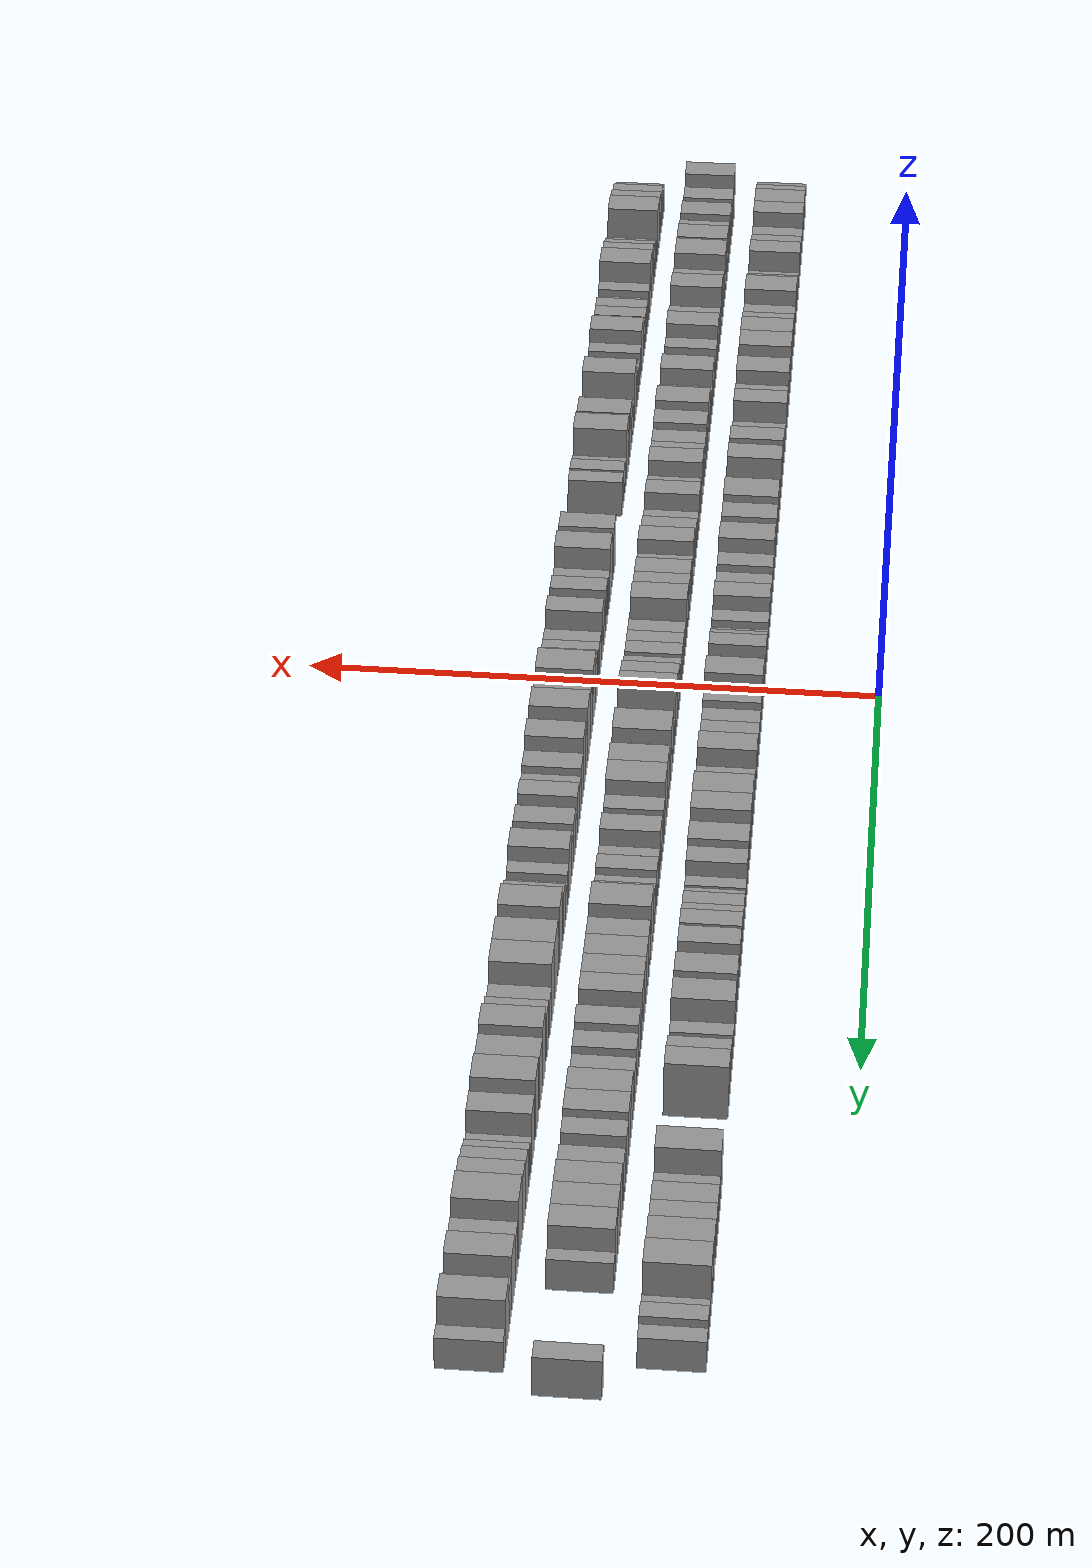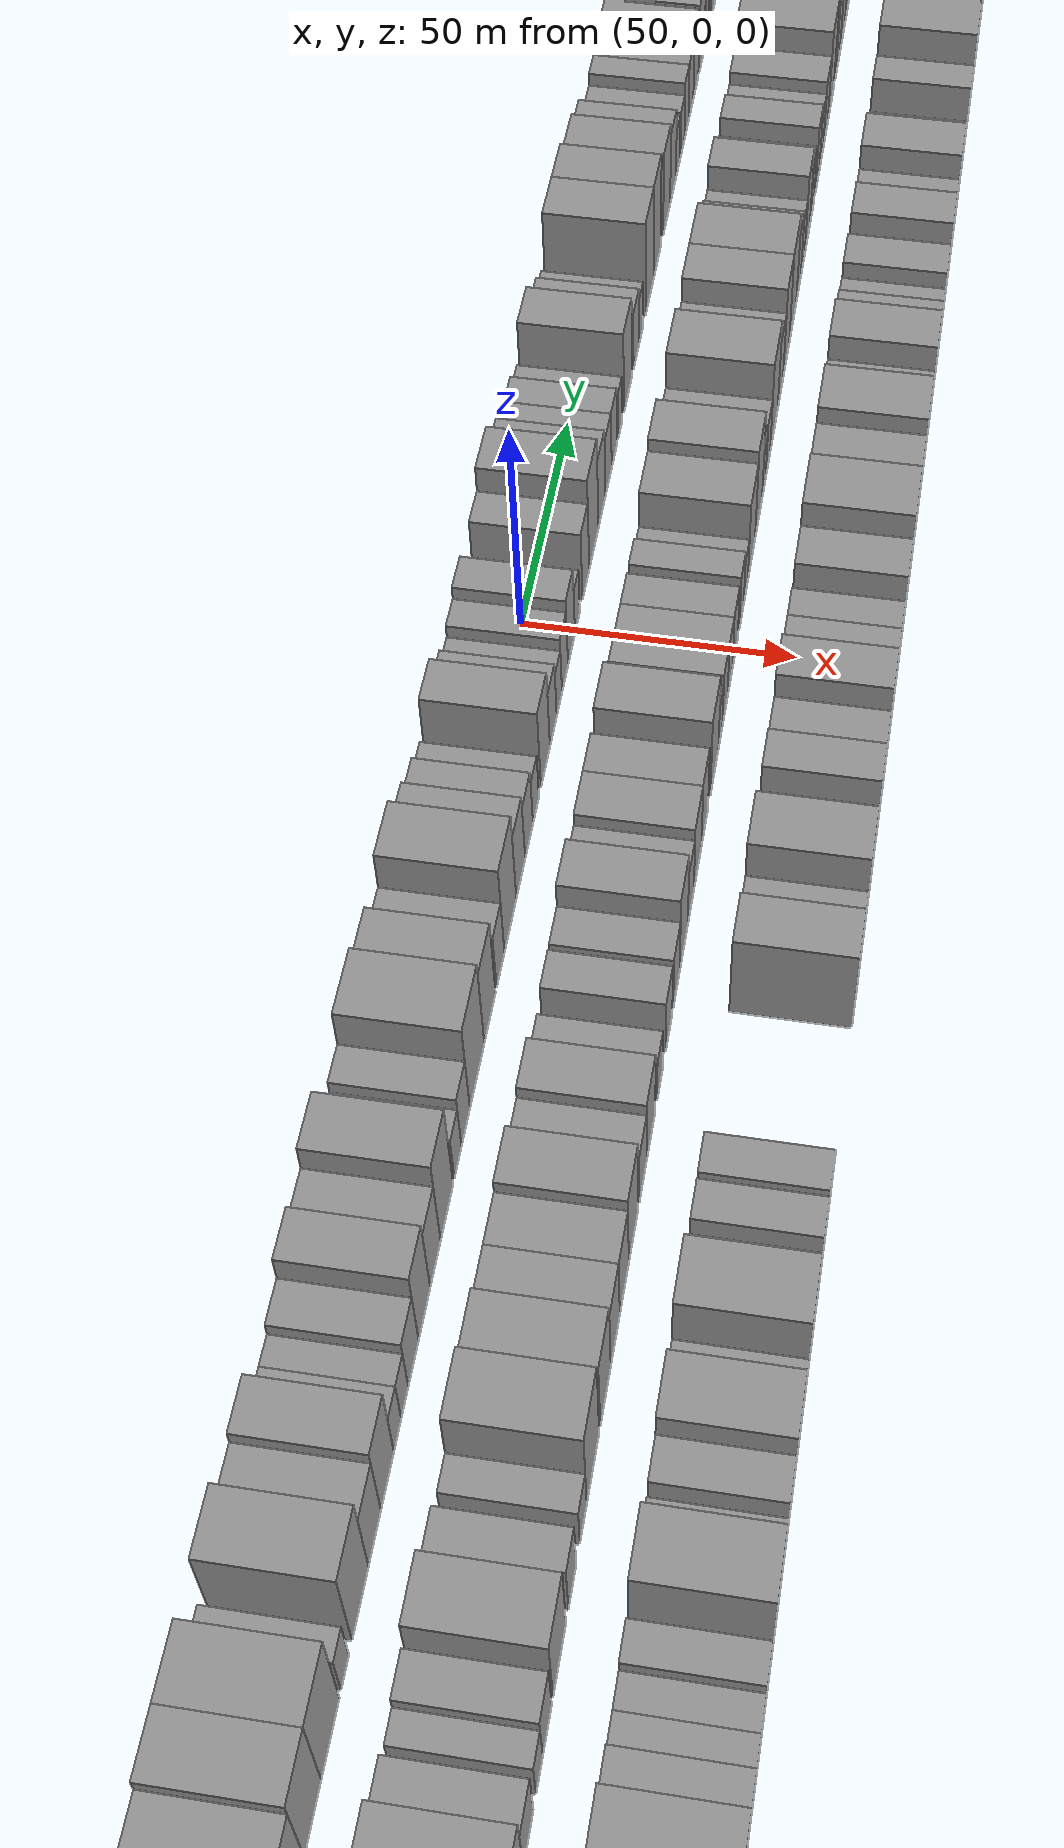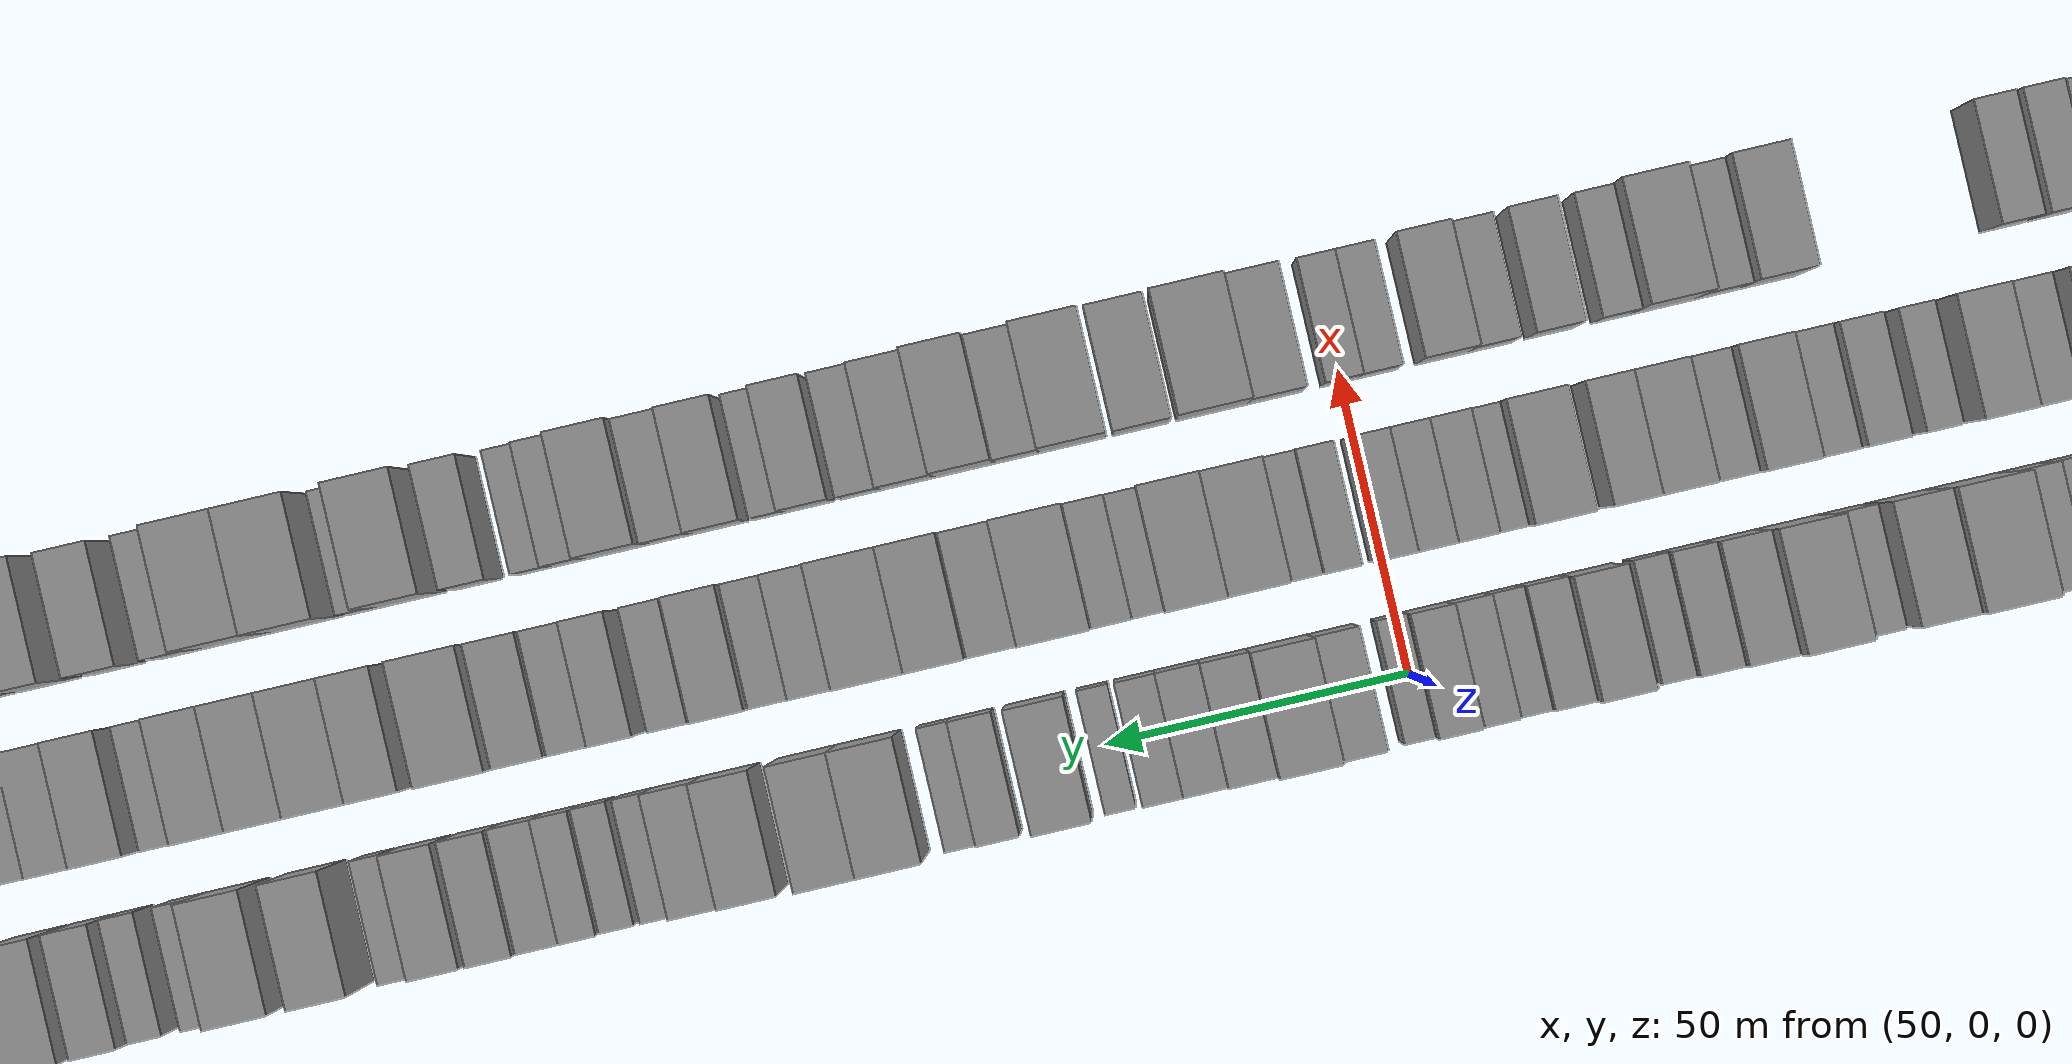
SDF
<sdf version="1.6">
 <world name="default">
  <scene>
   <sky><clouds><speed>12</speed></clouds></sky>
   <ambient>0.4 0.4 0.4 1</ambient>
   <background>0.7 0.7 0.7 1</background>
   <shadows>1</shadows>
  </scene>
  <gravity>0 0 -9.8066</gravity>
  <magnetic_field>6e-06 2.3e-05 -4.2e-05</magnetic_field>
  <physics default="0" name="default_physics" type="ode">
   <ode>
    <solver>
     <type>quick</type>
     <iters>10</iters>
     <sor>1.0</sor>
     <use_dynamic_moi_rescaling>0</use_dynamic_moi_rescaling>
    </solver>
    <constraints>
     <cfm>0</cfm>
     <erp>0.2</erp>
     <contact_max_correcting_vel>100</contact_max_correcting_vel>
     <contact_surface_layer>0.001</contact_surface_layer>
    </constraints>
   </ode>
   <max_step_size>0.004</max_step_size>
   <real_time_factor>1</real_time_factor>
   <real_time_update_rate>250</real_time_update_rate>
  </physics>
  <light name="sun" type="directional">
   <pose>0 0 10 0 0 0</pose>
   <diffuse>0.8 0.8 0.8 1</diffuse>
   <specular>0.2 0.2 0.2 1</specular>
   <attenuation>
    <range>1000</range>
    <constant>0.9</constant>
    <linear>0.01</linear>
    <quadratic>0.001</quadratic>
   </attenuation>
   <direction>-0.5 0.1 -0.9</direction>
  </light>
  <model name="building_1">
   <static>1</static>
   <pose>50.0000 -331.3577 0 0.000000 0.000000 0.000000</pose>
   <link name="link">
    <pose>0 0 7.50 0 0 0</pose>
    <collision name="collision"><geometry><box><size>20.0000 7.2847 15.0000</size></box></geometry></collision>
    <visual name="visual">
     <cast_shadows>0</cast_shadows>
     <geometry><box><size>20.0000 7.2847 15.0000</size></box></geometry>
     <material>
      <script>
       <uri>model://grey_wall/materials/scripts</uri>
       <uri>model://grey_wall/materials/textures</uri>
       <name>vrc/grey_wall</name>
      </script>
     </material>
    </visual>
   </link>
  </model>
  <model name="building_2">
   <static>1</static>
   <pose>50.0000 -323.3517 0 0.000000 0.000000 0.000000</pose>
   <link name="link">
    <pose>0 0 9.00 0 0 0</pose>
    <collision name="collision"><geometry><box><size>20.0000 8.7272 18.0000</size></box></geometry></collision>
    <visual name="visual">
     <cast_shadows>0</cast_shadows>
     <geometry><box><size>20.0000 8.7272 18.0000</size></box></geometry>
     <material>
      <script>
       <uri>model://grey_wall/materials/scripts</uri>
       <uri>model://grey_wall/materials/textures</uri>
       <name>vrc/grey_wall</name>
      </script>
     </material>
    </visual>
   </link>
  </model>
  <model name="building_3">
   <static>1</static>
   <pose>50.0000 -313.8566 0 0.000000 0.000000 0.000000</pose>
   <link name="link">
    <pose>0 0 10.50 0 0 0</pose>
    <collision name="collision"><geometry><box><size>20.0000 10.2631 21.0000</size></box></geometry></collision>
    <visual name="visual">
     <cast_shadows>0</cast_shadows>
     <geometry><box><size>20.0000 10.2631 21.0000</size></box></geometry>
     <material>
      <script>
       <uri>model://grey_wall/materials/scripts</uri>
       <uri>model://grey_wall/materials/textures</uri>
       <name>vrc/grey_wall</name>
      </script>
     </material>
    </visual>
   </link>
  </model>
  <model name="building_4">
   <static>1</static>
   <pose>50.0000 -304.1938 0 0.000000 0.000000 0.000000</pose>
   <link name="link">
    <pose>0 0 10.50 0 0 0</pose>
    <collision name="collision"><geometry><box><size>20.0000 9.0625 21.0000</size></box></geometry></collision>
    <visual name="visual">
     <cast_shadows>0</cast_shadows>
     <geometry><box><size>20.0000 9.0625 21.0000</size></box></geometry>
     <material>
      <script>
       <uri>model://grey_wall/materials/scripts</uri>
       <uri>model://grey_wall/materials/textures</uri>
       <name>vrc/grey_wall</name>
      </script>
     </material>
    </visual>
   </link>
  </model>
  <model name="building_5">
   <static>1</static>
   <pose>50.0000 -295.4204 0 0.000000 0.000000 0.000000</pose>
   <link name="link">
    <pose>0 0 7.50 0 0 0</pose>
    <collision name="collision"><geometry><box><size>20.0000 6.4842 15.0000</size></box></geometry></collision>
    <visual name="visual">
     <cast_shadows>0</cast_shadows>
     <geometry><box><size>20.0000 6.4842 15.0000</size></box></geometry>
     <material>
      <script>
       <uri>model://grey_wall/materials/scripts</uri>
       <uri>model://grey_wall/materials/textures</uri>
       <name>vrc/grey_wall</name>
      </script>
     </material>
    </visual>
   </link>
  </model>
  <model name="building_6">
   <static>1</static>
   <pose>50.0000 -289.1117 0 0.000000 0.000000 0.000000</pose>
   <link name="link">
    <pose>0 0 7.50 0 0 0</pose>
    <collision name="collision"><geometry><box><size>20.0000 6.1332 15.0000</size></box></geometry></collision>
    <visual name="visual">
     <cast_shadows>0</cast_shadows>
     <geometry><box><size>20.0000 6.1332 15.0000</size></box></geometry>
     <material>
      <script>
       <uri>model://grey_wall/materials/scripts</uri>
       <uri>model://grey_wall/materials/textures</uri>
       <name>vrc/grey_wall</name>
      </script>
     </material>
    </visual>
   </link>
  </model>
  <model name="building_7">
   <static>1</static>
   <pose>50.0000 -283.0841 0 0.000000 0.000000 0.000000</pose>
   <link name="link">
    <pose>0 0 6.00 0 0 0</pose>
    <collision name="collision"><geometry><box><size>20.0000 5.9221 12.0000</size></box></geometry></collision>
    <visual name="visual">
     <cast_shadows>0</cast_shadows>
     <geometry><box><size>20.0000 5.9221 12.0000</size></box></geometry>
     <material>
      <script>
       <uri>model://grey_wall/materials/scripts</uri>
       <uri>model://grey_wall/materials/textures</uri>
       <name>vrc/grey_wall</name>
      </script>
     </material>
    </visual>
   </link>
  </model>
  <model name="building_8">
   <static>1</static>
   <pose>50.0000 -272.7275 0 0.000000 0.000000 0.000000</pose>
   <link name="link">
    <pose>0 0 10.50 0 0 0</pose>
    <collision name="collision"><geometry><box><size>20.0000 8.7911 21.0000</size></box></geometry></collision>
    <visual name="visual">
     <cast_shadows>0</cast_shadows>
     <geometry><box><size>20.0000 8.7911 21.0000</size></box></geometry>
     <material>
      <script>
       <uri>model://grey_wall/materials/scripts</uri>
       <uri>model://grey_wall/materials/textures</uri>
       <name>vrc/grey_wall</name>
      </script>
     </material>
    </visual>
   </link>
  </model>
  <model name="building_9">
   <static>1</static>
   <pose>50.0000 -265.5425 0 0.000000 0.000000 0.000000</pose>
   <link name="link">
    <pose>0 0 6.00 0 0 0</pose>
    <collision name="collision"><geometry><box><size>20.0000 5.5788 12.0000</size></box></geometry></collision>
    <visual name="visual">
     <cast_shadows>0</cast_shadows>
     <geometry><box><size>20.0000 5.5788 12.0000</size></box></geometry>
     <material>
      <script>
       <uri>model://grey_wall/materials/scripts</uri>
       <uri>model://grey_wall/materials/textures</uri>
       <name>vrc/grey_wall</name>
      </script>
     </material>
    </visual>
   </link>
  </model>
  <model name="building_10">
   <static>1</static>
   <pose>50.0000 -259.7928 0 0.000000 0.000000 0.000000</pose>
   <link name="link">
    <pose>0 0 6.00 0 0 0</pose>
    <collision name="collision"><geometry><box><size>20.0000 5.9206 12.0000</size></box></geometry></collision>
    <visual name="visual">
     <cast_shadows>0</cast_shadows>
     <geometry><box><size>20.0000 5.9206 12.0000</size></box></geometry>
     <material>
      <script>
       <uri>model://grey_wall/materials/scripts</uri>
       <uri>model://grey_wall/materials/textures</uri>
       <name>vrc/grey_wall</name>
      </script>
     </material>
    </visual>
   </link>
  </model>
  <model name="building_11">
   <static>1</static>
   <pose>50.0000 -251.6989 0 0.000000 0.000000 0.000000</pose>
   <link name="link">
    <pose>0 0 9.00 0 0 0</pose>
    <collision name="collision"><geometry><box><size>20.0000 8.2673 18.0000</size></box></geometry></collision>
    <visual name="visual">
     <cast_shadows>0</cast_shadows>
     <geometry><box><size>20.0000 8.2673 18.0000</size></box></geometry>
     <material>
      <script>
       <uri>model://grey_wall/materials/scripts</uri>
       <uri>model://grey_wall/materials/textures</uri>
       <name>vrc/grey_wall</name>
      </script>
     </material>
    </visual>
   </link>
  </model>
  <model name="building_12">
   <static>1</static>
   <pose>50.0000 -238.9440 0 0.000000 0.000000 0.000000</pose>
   <link name="link">
    <pose>0 0 12.00 0 0 0</pose>
    <collision name="collision"><geometry><box><size>20.0000 11.2425 24.0000</size></box></geometry></collision>
    <visual name="visual">
     <cast_shadows>0</cast_shadows>
     <geometry><box><size>20.0000 11.2425 24.0000</size></box></geometry>
     <material>
      <script>
       <uri>model://grey_wall/materials/scripts</uri>
       <uri>model://grey_wall/materials/textures</uri>
       <name>vrc/grey_wall</name>
      </script>
     </material>
    </visual>
   </link>
  </model>
  <model name="building_13">
   <static>1</static>
   <pose>50.0000 -228.3245 0 0.000000 0.000000 0.000000</pose>
   <link name="link">
    <pose>0 0 9.00 0 0 0</pose>
    <collision name="collision"><geometry><box><size>20.0000 7.9965 18.0000</size></box></geometry></collision>
    <visual name="visual">
     <cast_shadows>0</cast_shadows>
     <geometry><box><size>20.0000 7.9965 18.0000</size></box></geometry>
     <material>
      <script>
       <uri>model://grey_wall/materials/scripts</uri>
       <uri>model://grey_wall/materials/textures</uri>
       <name>vrc/grey_wall</name>
      </script>
     </material>
    </visual>
   </link>
  </model>
  <model name="building_14">
   <static>1</static>
   <pose>50.0000 -217.0393 0 0.000000 0.000000 0.000000</pose>
   <link name="link">
    <pose>0 0 10.50 0 0 0</pose>
    <collision name="collision"><geometry><box><size>20.0000 8.5739 21.0000</size></box></geometry></collision>
    <visual name="visual">
     <cast_shadows>0</cast_shadows>
     <geometry><box><size>20.0000 8.5739 21.0000</size></box></geometry>
     <material>
      <script>
       <uri>model://grey_wall/materials/scripts</uri>
       <uri>model://grey_wall/materials/textures</uri>
       <name>vrc/grey_wall</name>
      </script>
     </material>
    </visual>
   </link>
  </model>
  <model name="building_15">
   <static>1</static>
   <pose>50.0000 -207.7493 0 0.000000 0.000000 0.000000</pose>
   <link name="link">
    <pose>0 0 12.00 0 0 0</pose>
    <collision name="collision"><geometry><box><size>20.0000 10.0060 24.0000</size></box></geometry></collision>
    <visual name="visual">
     <cast_shadows>0</cast_shadows>
     <geometry><box><size>20.0000 10.0060 24.0000</size></box></geometry>
     <material>
      <script>
       <uri>model://grey_wall/materials/scripts</uri>
       <uri>model://grey_wall/materials/textures</uri>
       <name>vrc/grey_wall</name>
      </script>
     </material>
    </visual>
   </link>
  </model>
  <model name="building_16">
   <static>1</static>
   <pose>50.0000 -197.1931 0 0.000000 0.000000 0.000000</pose>
   <link name="link">
    <pose>0 0 12.00 0 0 0</pose>
    <collision name="collision"><geometry><box><size>20.0000 11.1064 24.0000</size></box></geometry></collision>
    <visual name="visual">
     <cast_shadows>0</cast_shadows>
     <geometry><box><size>20.0000 11.1064 24.0000</size></box></geometry>
     <material>
      <script>
       <uri>model://grey_wall/materials/scripts</uri>
       <uri>model://grey_wall/materials/textures</uri>
       <name>vrc/grey_wall</name>
      </script>
     </material>
    </visual>
   </link>
  </model>
  <model name="building_17">
   <static>1</static>
   <pose>50.0000 -188.1655 0 0.000000 0.000000 0.000000</pose>
   <link name="link">
    <pose>0 0 6.00 0 0 0</pose>
    <collision name="collision"><geometry><box><size>20.0000 4.9488 12.0000</size></box></geometry></collision>
    <visual name="visual">
     <cast_shadows>0</cast_shadows>
     <geometry><box><size>20.0000 4.9488 12.0000</size></box></geometry>
     <material>
      <script>
       <uri>model://grey_wall/materials/scripts</uri>
       <uri>model://grey_wall/materials/textures</uri>
       <name>vrc/grey_wall</name>
      </script>
     </material>
    </visual>
   </link>
  </model>
  <model name="building_18">
   <static>1</static>
   <pose>50.0000 -178.3709 0 0.000000 0.000000 0.000000</pose>
   <link name="link">
    <pose>0 0 12.00 0 0 0</pose>
    <collision name="collision"><geometry><box><size>20.0000 10.6405 24.0000</size></box></geometry></collision>
    <visual name="visual">
     <cast_shadows>0</cast_shadows>
     <geometry><box><size>20.0000 10.6405 24.0000</size></box></geometry>
     <material>
      <script>
       <uri>model://grey_wall/materials/scripts</uri>
       <uri>model://grey_wall/materials/textures</uri>
       <name>vrc/grey_wall</name>
      </script>
     </material>
    </visual>
   </link>
  </model>
  <model name="building_19">
   <static>1</static>
   <pose>50.0000 -168.9221 0 0.000000 0.000000 0.000000</pose>
   <link name="link">
    <pose>0 0 9.00 0 0 0</pose>
    <collision name="collision"><geometry><box><size>20.0000 8.2570 18.0000</size></box></geometry></collision>
    <visual name="visual">
     <cast_shadows>0</cast_shadows>
     <geometry><box><size>20.0000 8.2570 18.0000</size></box></geometry>
     <material>
      <script>
       <uri>model://grey_wall/materials/scripts</uri>
       <uri>model://grey_wall/materials/textures</uri>
       <name>vrc/grey_wall</name>
      </script>
     </material>
    </visual>
   </link>
  </model>
  <model name="building_20">
   <static>1</static>
   <pose>50.0000 -160.3604 0 0.000000 0.000000 0.000000</pose>
   <link name="link">
    <pose>0 0 10.50 0 0 0</pose>
    <collision name="collision"><geometry><box><size>20.0000 8.8665 21.0000</size></box></geometry></collision>
    <visual name="visual">
     <cast_shadows>0</cast_shadows>
     <geometry><box><size>20.0000 8.8665 21.0000</size></box></geometry>
     <material>
      <script>
       <uri>model://grey_wall/materials/scripts</uri>
       <uri>model://grey_wall/materials/textures</uri>
       <name>vrc/grey_wall</name>
      </script>
     </material>
    </visual>
   </link>
  </model>
  <model name="building_21">
   <static>1</static>
   <pose>50.0000 -153.3764 0 0.000000 0.000000 0.000000</pose>
   <link name="link">
    <pose>0 0 6.00 0 0 0</pose>
    <collision name="collision"><geometry><box><size>20.0000 5.1015 12.0000</size></box></geometry></collision>
    <visual name="visual">
     <cast_shadows>0</cast_shadows>
     <geometry><box><size>20.0000 5.1015 12.0000</size></box></geometry>
     <material>
      <script>
       <uri>model://grey_wall/materials/scripts</uri>
       <uri>model://grey_wall/materials/textures</uri>
       <name>vrc/grey_wall</name>
      </script>
     </material>
    </visual>
   </link>
  </model>
  <model name="building_22">
   <static>1</static>
   <pose>50.0000 -148.3081 0 0.000000 0.000000 0.000000</pose>
   <link name="link">
    <pose>0 0 6.00 0 0 0</pose>
    <collision name="collision"><geometry><box><size>20.0000 5.0352 12.0000</size></box></geometry></collision>
    <visual name="visual">
     <cast_shadows>0</cast_shadows>
     <geometry><box><size>20.0000 5.0352 12.0000</size></box></geometry>
     <material>
      <script>
       <uri>model://grey_wall/materials/scripts</uri>
       <uri>model://grey_wall/materials/textures</uri>
       <name>vrc/grey_wall</name>
      </script>
     </material>
    </visual>
   </link>
  </model>
  <model name="building_23">
   <static>1</static>
   <pose>50.0000 -142.0595 0 0.000000 0.000000 0.000000</pose>
   <link name="link">
    <pose>0 0 7.50 0 0 0</pose>
    <collision name="collision"><geometry><box><size>20.0000 7.4621 15.0000</size></box></geometry></collision>
    <visual name="visual">
     <cast_shadows>0</cast_shadows>
     <geometry><box><size>20.0000 7.4621 15.0000</size></box></geometry>
     <material>
      <script>
       <uri>model://grey_wall/materials/scripts</uri>
       <uri>model://grey_wall/materials/textures</uri>
       <name>vrc/grey_wall</name>
      </script>
     </material>
    </visual>
   </link>
  </model>
  <model name="building_24">
   <static>1</static>
   <pose>50.0000 -134.0464 0 0.000000 0.000000 0.000000</pose>
   <link name="link">
    <pose>0 0 10.50 0 0 0</pose>
    <collision name="collision"><geometry><box><size>20.0000 8.5641 21.0000</size></box></geometry></collision>
    <visual name="visual">
     <cast_shadows>0</cast_shadows>
     <geometry><box><size>20.0000 8.5641 21.0000</size></box></geometry>
     <material>
      <script>
       <uri>model://grey_wall/materials/scripts</uri>
       <uri>model://grey_wall/materials/textures</uri>
       <name>vrc/grey_wall</name>
      </script>
     </material>
    </visual>
   </link>
  </model>
  <model name="building_25">
   <static>1</static>
   <pose>50.0000 -125.8016 0 0.000000 0.000000 0.000000</pose>
   <link name="link">
    <pose>0 0 9.00 0 0 0</pose>
    <collision name="collision"><geometry><box><size>20.0000 7.9255 18.0000</size></box></geometry></collision>
    <visual name="visual">
     <cast_shadows>0</cast_shadows>
     <geometry><box><size>20.0000 7.9255 18.0000</size></box></geometry>
     <material>
      <script>
       <uri>model://grey_wall/materials/scripts</uri>
       <uri>model://grey_wall/materials/textures</uri>
       <name>vrc/grey_wall</name>
      </script>
     </material>
    </visual>
   </link>
  </model>
  <model name="building_26">
   <static>1</static>
   <pose>50.0000 -116.9919 0 0.000000 0.000000 0.000000</pose>
   <link name="link">
    <pose>0 0 12.00 0 0 0</pose>
    <collision name="collision"><geometry><box><size>20.0000 9.6940 24.0000</size></box></geometry></collision>
    <visual name="visual">
     <cast_shadows>0</cast_shadows>
     <geometry><box><size>20.0000 9.6940 24.0000</size></box></geometry>
     <material>
      <script>
       <uri>model://grey_wall/materials/scripts</uri>
       <uri>model://grey_wall/materials/textures</uri>
       <name>vrc/grey_wall</name>
      </script>
     </material>
    </visual>
   </link>
  </model>
  <model name="building_27">
   <static>1</static>
   <pose>50.0000 -108.3134 0 0.000000 0.000000 0.000000</pose>
   <link name="link">
    <pose>0 0 6.00 0 0 0</pose>
    <collision name="collision"><geometry><box><size>20.0000 5.6629 12.0000</size></box></geometry></collision>
    <visual name="visual">
     <cast_shadows>0</cast_shadows>
     <geometry><box><size>20.0000 5.6629 12.0000</size></box></geometry>
     <material>
      <script>
       <uri>model://grey_wall/materials/scripts</uri>
       <uri>model://grey_wall/materials/textures</uri>
       <name>vrc/grey_wall</name>
      </script>
     </material>
    </visual>
   </link>
  </model>
  <model name="building_28">
   <static>1</static>
   <pose>50.0000 -102.0696 0 0.000000 0.000000 0.000000</pose>
   <link name="link">
    <pose>0 0 7.50 0 0 0</pose>
    <collision name="collision"><geometry><box><size>20.0000 6.8247 15.0000</size></box></geometry></collision>
    <visual name="visual">
     <cast_shadows>0</cast_shadows>
     <geometry><box><size>20.0000 6.8247 15.0000</size></box></geometry>
     <material>
      <script>
       <uri>model://grey_wall/materials/scripts</uri>
       <uri>model://grey_wall/materials/textures</uri>
       <name>vrc/grey_wall</name>
      </script>
     </material>
    </visual>
   </link>
  </model>
  <model name="building_29">
   <static>1</static>
   <pose>50.0000 -92.6623 0 0.000000 0.000000 0.000000</pose>
   <link name="link">
    <pose>0 0 12.00 0 0 0</pose>
    <collision name="collision"><geometry><box><size>20.0000 11.9899 24.0000</size></box></geometry></collision>
    <visual name="visual">
     <cast_shadows>0</cast_shadows>
     <geometry><box><size>20.0000 11.9899 24.0000</size></box></geometry>
     <material>
      <script>
       <uri>model://grey_wall/materials/scripts</uri>
       <uri>model://grey_wall/materials/textures</uri>
       <name>vrc/grey_wall</name>
      </script>
     </material>
    </visual>
   </link>
  </model>
  <model name="building_30">
   <static>1</static>
   <pose>50.0000 -81.8730 0 0.000000 0.000000 0.000000</pose>
   <link name="link">
    <pose>0 0 10.50 0 0 0</pose>
    <collision name="collision"><geometry><box><size>20.0000 9.5886 21.0000</size></box></geometry></collision>
    <visual name="visual">
     <cast_shadows>0</cast_shadows>
     <geometry><box><size>20.0000 9.5886 21.0000</size></box></geometry>
     <material>
      <script>
       <uri>model://grey_wall/materials/scripts</uri>
       <uri>model://grey_wall/materials/textures</uri>
       <name>vrc/grey_wall</name>
      </script>
     </material>
    </visual>
   </link>
  </model>
  <model name="building_31">
   <static>1</static>
   <pose>50.0000 -72.6580 0 0.000000 0.000000 0.000000</pose>
   <link name="link">
    <pose>0 0 7.50 0 0 0</pose>
    <collision name="collision"><geometry><box><size>20.0000 6.8415 15.0000</size></box></geometry></collision>
    <visual name="visual">
     <cast_shadows>0</cast_shadows>
     <geometry><box><size>20.0000 6.8415 15.0000</size></box></geometry>
     <material>
      <script>
       <uri>model://grey_wall/materials/scripts</uri>
       <uri>model://grey_wall/materials/textures</uri>
       <name>vrc/grey_wall</name>
      </script>
     </material>
    </visual>
   </link>
  </model>
  <model name="building_32">
   <static>1</static>
   <pose>50.0000 -63.8661 0 0.000000 0.000000 0.000000</pose>
   <link name="link">
    <pose>0 0 12.00 0 0 0</pose>
    <collision name="collision"><geometry><box><size>20.0000 10.7423 24.0000</size></box></geometry></collision>
    <visual name="visual">
     <cast_shadows>0</cast_shadows>
     <geometry><box><size>20.0000 10.7423 24.0000</size></box></geometry>
     <material>
      <script>
       <uri>model://grey_wall/materials/scripts</uri>
       <uri>model://grey_wall/materials/textures</uri>
       <name>vrc/grey_wall</name>
      </script>
     </material>
    </visual>
   </link>
  </model>
  <model name="building_33">
   <static>1</static>
   <pose>50.0000 -54.4103 0 0.000000 0.000000 0.000000</pose>
   <link name="link">
    <pose>0 0 9.00 0 0 0</pose>
    <collision name="collision"><geometry><box><size>20.0000 8.1693 18.0000</size></box></geometry></collision>
    <visual name="visual">
     <cast_shadows>0</cast_shadows>
     <geometry><box><size>20.0000 8.1693 18.0000</size></box></geometry>
     <material>
      <script>
       <uri>model://grey_wall/materials/scripts</uri>
       <uri>model://grey_wall/materials/textures</uri>
       <name>vrc/grey_wall</name>
      </script>
     </material>
    </visual>
   </link>
  </model>
  <model name="building_34">
   <static>1</static>
   <pose>50.0000 -46.6696 0 0.000000 0.000000 0.000000</pose>
   <link name="link">
    <pose>0 0 7.50 0 0 0</pose>
    <collision name="collision"><geometry><box><size>20.0000 7.3122 15.0000</size></box></geometry></collision>
    <visual name="visual">
     <cast_shadows>0</cast_shadows>
     <geometry><box><size>20.0000 7.3122 15.0000</size></box></geometry>
     <material>
      <script>
       <uri>model://grey_wall/materials/scripts</uri>
       <uri>model://grey_wall/materials/textures</uri>
       <name>vrc/grey_wall</name>
      </script>
     </material>
    </visual>
   </link>
  </model>
  <model name="building_35">
   <static>1</static>
   <pose>50.0000 -40.1810 0 0.000000 0.000000 0.000000</pose>
   <link name="link">
    <pose>0 0 6.00 0 0 0</pose>
    <collision name="collision"><geometry><box><size>20.0000 5.6649 12.0000</size></box></geometry></collision>
    <visual name="visual">
     <cast_shadows>0</cast_shadows>
     <geometry><box><size>20.0000 5.6649 12.0000</size></box></geometry>
     <material>
      <script>
       <uri>model://grey_wall/materials/scripts</uri>
       <uri>model://grey_wall/materials/textures</uri>
       <name>vrc/grey_wall</name>
      </script>
     </material>
    </visual>
   </link>
  </model>
  <model name="building_36">
   <static>1</static>
   <pose>50.0000 -30.9514 0 0.000000 0.000000 0.000000</pose>
   <link name="link">
    <pose>0 0 10.50 0 0 0</pose>
    <collision name="collision"><geometry><box><size>20.0000 8.7943 21.0000</size></box></geometry></collision>
    <visual name="visual">
     <cast_shadows>0</cast_shadows>
     <geometry><box><size>20.0000 8.7943 21.0000</size></box></geometry>
     <material>
      <script>
       <uri>model://grey_wall/materials/scripts</uri>
       <uri>model://grey_wall/materials/textures</uri>
       <name>vrc/grey_wall</name>
      </script>
     </material>
    </visual>
   </link>
  </model>
  <model name="building_37">
   <static>1</static>
   <pose>50.0000 -23.1737 0 0.000000 0.000000 0.000000</pose>
   <link name="link">
    <pose>0 0 7.50 0 0 0</pose>
    <collision name="collision"><geometry><box><size>20.0000 6.7610 15.0000</size></box></geometry></collision>
    <visual name="visual">
     <cast_shadows>0</cast_shadows>
     <geometry><box><size>20.0000 6.7610 15.0000</size></box></geometry>
     <material>
      <script>
       <uri>model://grey_wall/materials/scripts</uri>
       <uri>model://grey_wall/materials/textures</uri>
       <name>vrc/grey_wall</name>
      </script>
     </material>
    </visual>
   </link>
  </model>
  <model name="building_38">
   <static>1</static>
   <pose>50.0000 -17.0934 0 0.000000 0.000000 0.000000</pose>
   <link name="link">
    <pose>0 0 6.00 0 0 0</pose>
    <collision name="collision"><geometry><box><size>20.0000 5.3997 12.0000</size></box></geometry></collision>
    <visual name="visual">
     <cast_shadows>0</cast_shadows>
     <geometry><box><size>20.0000 5.3997 12.0000</size></box></geometry>
     <material>
      <script>
       <uri>model://grey_wall/materials/scripts</uri>
       <uri>model://grey_wall/materials/textures</uri>
       <name>vrc/grey_wall</name>
      </script>
     </material>
    </visual>
   </link>
  </model>
  <model name="building_39">
   <static>1</static>
   <pose>50.0000 -11.2856 0 0.000000 0.000000 0.000000</pose>
   <link name="link">
    <pose>0 0 7.50 0 0 0</pose>
    <collision name="collision"><geometry><box><size>20.0000 6.2158 15.0000</size></box></geometry></collision>
    <visual name="visual">
     <cast_shadows>0</cast_shadows>
     <geometry><box><size>20.0000 6.2158 15.0000</size></box></geometry>
     <material>
      <script>
       <uri>model://grey_wall/materials/scripts</uri>
       <uri>model://grey_wall/materials/textures</uri>
       <name>vrc/grey_wall</name>
      </script>
     </material>
    </visual>
   </link>
  </model>
  <model name="building_40">
   <static>1</static>
   <pose>50.0000 -4.5545 0 0.000000 0.000000 0.000000</pose>
   <link name="link">
    <pose>0 0 9.00 0 0 0</pose>
    <collision name="collision"><geometry><box><size>20.0000 7.2465 18.0000</size></box></geometry></collision>
    <visual name="visual">
     <cast_shadows>0</cast_shadows>
     <geometry><box><size>20.0000 7.2465 18.0000</size></box></geometry>
     <material>
      <script>
       <uri>model://grey_wall/materials/scripts</uri>
       <uri>model://grey_wall/materials/textures</uri>
       <name>vrc/grey_wall</name>
      </script>
     </material>
    </visual>
   </link>
  </model>
  <model name="building_41">
   <static>1</static>
   <pose>50.0000 1.6012 0 0.000000 0.000000 0.000000</pose>
   <link name="link">
    <pose>0 0 6.00 0 0 0</pose>
    <collision name="collision"><geometry><box><size>20.0000 5.0649 12.0000</size></box></geometry></collision>
    <visual name="visual">
     <cast_shadows>0</cast_shadows>
     <geometry><box><size>20.0000 5.0649 12.0000</size></box></geometry>
     <material>
      <script>
       <uri>model://grey_wall/materials/scripts</uri>
       <uri>model://grey_wall/materials/textures</uri>
       <name>vrc/grey_wall</name>
      </script>
     </material>
    </visual>
   </link>
  </model>
  <model name="building_42">
   <static>1</static>
   <pose>50.0000 10.8455 0 0.000000 0.000000 0.000000</pose>
   <link name="link">
    <pose>0 0 9.00 0 0 0</pose>
    <collision name="collision"><geometry><box><size>20.0000 7.4237 18.0000</size></box></geometry></collision>
    <visual name="visual">
     <cast_shadows>0</cast_shadows>
     <geometry><box><size>20.0000 7.4237 18.0000</size></box></geometry>
     <material>
      <script>
       <uri>model://grey_wall/materials/scripts</uri>
       <uri>model://grey_wall/materials/textures</uri>
       <name>vrc/grey_wall</name>
      </script>
     </material>
    </visual>
   </link>
  </model>
  <model name="building_43">
   <static>1</static>
   <pose>50.0000 19.6524 0 0.000000 0.000000 0.000000</pose>
   <link name="link">
    <pose>0 0 12.00 0 0 0</pose>
    <collision name="collision"><geometry><box><size>20.0000 10.1900 24.0000</size></box></geometry></collision>
    <visual name="visual">
     <cast_shadows>0</cast_shadows>
     <geometry><box><size>20.0000 10.1900 24.0000</size></box></geometry>
     <material>
      <script>
       <uri>model://grey_wall/materials/scripts</uri>
       <uri>model://grey_wall/materials/textures</uri>
       <name>vrc/grey_wall</name>
      </script>
     </material>
    </visual>
   </link>
  </model>
  <model name="building_44">
   <static>1</static>
   <pose>50.0000 28.7017 0 0.000000 0.000000 0.000000</pose>
   <link name="link">
    <pose>0 0 9.00 0 0 0</pose>
    <collision name="collision"><geometry><box><size>20.0000 7.9085 18.0000</size></box></geometry></collision>
    <visual name="visual">
     <cast_shadows>0</cast_shadows>
     <geometry><box><size>20.0000 7.9085 18.0000</size></box></geometry>
     <material>
      <script>
       <uri>model://grey_wall/materials/scripts</uri>
       <uri>model://grey_wall/materials/textures</uri>
       <name>vrc/grey_wall</name>
      </script>
     </material>
    </visual>
   </link>
  </model>
  <model name="building_45">
   <static>1</static>
   <pose>50.0000 36.2491 0 0.000000 0.000000 0.000000</pose>
   <link name="link">
    <pose>0 0 7.50 0 0 0</pose>
    <collision name="collision"><geometry><box><size>20.0000 7.1863 15.0000</size></box></geometry></collision>
    <visual name="visual">
     <cast_shadows>0</cast_shadows>
     <geometry><box><size>20.0000 7.1863 15.0000</size></box></geometry>
     <material>
      <script>
       <uri>model://grey_wall/materials/scripts</uri>
       <uri>model://grey_wall/materials/textures</uri>
       <name>vrc/grey_wall</name>
      </script>
     </material>
    </visual>
   </link>
  </model>
  <model name="building_46">
   <static>1</static>
   <pose>50.0000 43.0937 0 0.000000 0.000000 0.000000</pose>
   <link name="link">
    <pose>0 0 7.50 0 0 0</pose>
    <collision name="collision"><geometry><box><size>20.0000 6.5029 15.0000</size></box></geometry></collision>
    <visual name="visual">
     <cast_shadows>0</cast_shadows>
     <geometry><box><size>20.0000 6.5029 15.0000</size></box></geometry>
     <material>
      <script>
       <uri>model://grey_wall/materials/scripts</uri>
       <uri>model://grey_wall/materials/textures</uri>
       <name>vrc/grey_wall</name>
      </script>
     </material>
    </visual>
   </link>
  </model>
  <model name="building_47">
   <static>1</static>
   <pose>50.0000 49.8750 0 0.000000 0.000000 0.000000</pose>
   <link name="link">
    <pose>0 0 6.00 0 0 0</pose>
    <collision name="collision"><geometry><box><size>20.0000 5.0597 12.0000</size></box></geometry></collision>
    <visual name="visual">
     <cast_shadows>0</cast_shadows>
     <geometry><box><size>20.0000 5.0597 12.0000</size></box></geometry>
     <material>
      <script>
       <uri>model://grey_wall/materials/scripts</uri>
       <uri>model://grey_wall/materials/textures</uri>
       <name>vrc/grey_wall</name>
      </script>
     </material>
    </visual>
   </link>
  </model>
  <model name="building_48">
   <static>1</static>
   <pose>50.0000 59.2277 0 0.000000 0.000000 0.000000</pose>
   <link name="link">
    <pose>0 0 10.50 0 0 0</pose>
    <collision name="collision"><geometry><box><size>20.0000 9.6456 21.0000</size></box></geometry></collision>
    <visual name="visual">
     <cast_shadows>0</cast_shadows>
     <geometry><box><size>20.0000 9.6456 21.0000</size></box></geometry>
     <material>
      <script>
       <uri>model://grey_wall/materials/scripts</uri>
       <uri>model://grey_wall/materials/textures</uri>
       <name>vrc/grey_wall</name>
      </script>
     </material>
    </visual>
   </link>
  </model>
  <model name="building_49">
   <static>1</static>
   <pose>50.0000 69.5857 0 0.000000 0.000000 0.000000</pose>
   <link name="link">
    <pose>0 0 7.50 0 0 0</pose>
    <collision name="collision"><geometry><box><size>20.0000 7.0703 15.0000</size></box></geometry></collision>
    <visual name="visual">
     <cast_shadows>0</cast_shadows>
     <geometry><box><size>20.0000 7.0703 15.0000</size></box></geometry>
     <material>
      <script>
       <uri>model://grey_wall/materials/scripts</uri>
       <uri>model://grey_wall/materials/textures</uri>
       <name>vrc/grey_wall</name>
      </script>
     </material>
    </visual>
   </link>
  </model>
  <model name="building_50">
   <static>1</static>
   <pose>50.0000 75.6747 0 0.000000 0.000000 0.000000</pose>
   <link name="link">
    <pose>0 0 6.00 0 0 0</pose>
    <collision name="collision"><geometry><box><size>20.0000 5.1077 12.0000</size></box></geometry></collision>
    <visual name="visual">
     <cast_shadows>0</cast_shadows>
     <geometry><box><size>20.0000 5.1077 12.0000</size></box></geometry>
     <material>
      <script>
       <uri>model://grey_wall/materials/scripts</uri>
       <uri>model://grey_wall/materials/textures</uri>
       <name>vrc/grey_wall</name>
      </script>
     </material>
    </visual>
   </link>
  </model>
  <model name="building_51">
   <static>1</static>
   <pose>50.0000 86.4801 0 0.000000 0.000000 0.000000</pose>
   <link name="link">
    <pose>0 0 12.00 0 0 0</pose>
    <collision name="collision"><geometry><box><size>20.0000 10.5031 24.0000</size></box></geometry></collision>
    <visual name="visual">
     <cast_shadows>0</cast_shadows>
     <geometry><box><size>20.0000 10.5031 24.0000</size></box></geometry>
     <material>
      <script>
       <uri>model://grey_wall/materials/scripts</uri>
       <uri>model://grey_wall/materials/textures</uri>
       <name>vrc/grey_wall</name>
      </script>
     </material>
    </visual>
   </link>
  </model>
  <model name="building_52">
   <static>1</static>
   <pose>50.0000 96.5732 0 0.000000 0.000000 0.000000</pose>
   <link name="link">
    <pose>0 0 12.00 0 0 0</pose>
    <collision name="collision"><geometry><box><size>20.0000 9.6831 24.0000</size></box></geometry></collision>
    <visual name="visual">
     <cast_shadows>0</cast_shadows>
     <geometry><box><size>20.0000 9.6831 24.0000</size></box></geometry>
     <material>
      <script>
       <uri>model://grey_wall/materials/scripts</uri>
       <uri>model://grey_wall/materials/textures</uri>
       <name>vrc/grey_wall</name>
      </script>
     </material>
    </visual>
   </link>
  </model>
  <model name="building_53">
   <static>1</static>
   <pose>50.0000 109.1730 0 0.000000 0.000000 0.000000</pose>
   <link name="link">
    <pose>0 0 10.50 0 0 0</pose>
    <collision name="collision"><geometry><box><size>20.0000 9.5166 21.0000</size></box></geometry></collision>
    <visual name="visual">
     <cast_shadows>0</cast_shadows>
     <geometry><box><size>20.0000 9.5166 21.0000</size></box></geometry>
     <material>
      <script>
       <uri>model://grey_wall/materials/scripts</uri>
       <uri>model://grey_wall/materials/textures</uri>
       <name>vrc/grey_wall</name>
      </script>
     </material>
    </visual>
   </link>
  </model>
  <model name="building_54">
   <static>1</static>
   <pose>50.0000 117.9584 0 0.000000 0.000000 0.000000</pose>
   <link name="link">
    <pose>0 0 9.00 0 0 0</pose>
    <collision name="collision"><geometry><box><size>20.0000 8.0541 18.0000</size></box></geometry></collision>
    <visual name="visual">
     <cast_shadows>0</cast_shadows>
     <geometry><box><size>20.0000 8.0541 18.0000</size></box></geometry>
     <material>
      <script>
       <uri>model://grey_wall/materials/scripts</uri>
       <uri>model://grey_wall/materials/textures</uri>
       <name>vrc/grey_wall</name>
      </script>
     </material>
    </visual>
   </link>
  </model>
  <model name="building_55">
   <static>1</static>
   <pose>50.0000 124.6150 0 0.000000 0.000000 0.000000</pose>
   <link name="link">
    <pose>0 0 6.00 0 0 0</pose>
    <collision name="collision"><geometry><box><size>20.0000 5.2591 12.0000</size></box></geometry></collision>
    <visual name="visual">
     <cast_shadows>0</cast_shadows>
     <geometry><box><size>20.0000 5.2591 12.0000</size></box></geometry>
     <material>
      <script>
       <uri>model://grey_wall/materials/scripts</uri>
       <uri>model://grey_wall/materials/textures</uri>
       <name>vrc/grey_wall</name>
      </script>
     </material>
    </visual>
   </link>
  </model>
  <model name="building_56">
   <static>1</static>
   <pose>50.0000 131.0785 0 0.000000 0.000000 0.000000</pose>
   <link name="link">
    <pose>0 0 6.00 0 0 0</pose>
    <collision name="collision"><geometry><box><size>20.0000 5.6680 12.0000</size></box></geometry></collision>
    <visual name="visual">
     <cast_shadows>0</cast_shadows>
     <geometry><box><size>20.0000 5.6680 12.0000</size></box></geometry>
     <material>
      <script>
       <uri>model://grey_wall/materials/scripts</uri>
       <uri>model://grey_wall/materials/textures</uri>
       <name>vrc/grey_wall</name>
      </script>
     </material>
    </visual>
   </link>
  </model>
  <model name="building_57">
   <static>1</static>
   <pose>50.0000 136.9434 0 0.000000 0.000000 0.000000</pose>
   <link name="link">
    <pose>0 0 7.50 0 0 0</pose>
    <collision name="collision"><geometry><box><size>20.0000 6.0618 15.0000</size></box></geometry></collision>
    <visual name="visual">
     <cast_shadows>0</cast_shadows>
     <geometry><box><size>20.0000 6.0618 15.0000</size></box></geometry>
     <material>
      <script>
       <uri>model://grey_wall/materials/scripts</uri>
       <uri>model://grey_wall/materials/textures</uri>
       <name>vrc/grey_wall</name>
      </script>
     </material>
    </visual>
   </link>
  </model>
  <model name="building_58">
   <static>1</static>
   <pose>50.0000 143.4078 0 0.000000 0.000000 0.000000</pose>
   <link name="link">
    <pose>0 0 7.50 0 0 0</pose>
    <collision name="collision"><geometry><box><size>20.0000 6.8670 15.0000</size></box></geometry></collision>
    <visual name="visual">
     <cast_shadows>0</cast_shadows>
     <geometry><box><size>20.0000 6.8670 15.0000</size></box></geometry>
     <material>
      <script>
       <uri>model://grey_wall/materials/scripts</uri>
       <uri>model://grey_wall/materials/textures</uri>
       <name>vrc/grey_wall</name>
      </script>
     </material>
    </visual>
   </link>
  </model>
  <model name="building_59">
   <static>1</static>
   <pose>50.0000 150.5706 0 0.000000 0.000000 0.000000</pose>
   <link name="link">
    <pose>0 0 9.00 0 0 0</pose>
    <collision name="collision"><geometry><box><size>20.0000 7.4586 18.0000</size></box></geometry></collision>
    <visual name="visual">
     <cast_shadows>0</cast_shadows>
     <geometry><box><size>20.0000 7.4586 18.0000</size></box></geometry>
     <material>
      <script>
       <uri>model://grey_wall/materials/scripts</uri>
       <uri>model://grey_wall/materials/textures</uri>
       <name>vrc/grey_wall</name>
      </script>
     </material>
    </visual>
   </link>
  </model>
  <model name="building_60">
   <static>1</static>
   <pose>50.0000 159.4601 0 0.000000 0.000000 0.000000</pose>
   <link name="link">
    <pose>0 0 9.00 0 0 0</pose>
    <collision name="collision"><geometry><box><size>20.0000 8.3203 18.0000</size></box></geometry></collision>
    <visual name="visual">
     <cast_shadows>0</cast_shadows>
     <geometry><box><size>20.0000 8.3203 18.0000</size></box></geometry>
     <material>
      <script>
       <uri>model://grey_wall/materials/scripts</uri>
       <uri>model://grey_wall/materials/textures</uri>
       <name>vrc/grey_wall</name>
      </script>
     </material>
    </visual>
   </link>
  </model>
  <model name="building_61">
   <static>1</static>
   <pose>50.0000 167.0739 0 0.000000 0.000000 0.000000</pose>
   <link name="link">
    <pose>0 0 6.00 0 0 0</pose>
    <collision name="collision"><geometry><box><size>20.0000 4.9073 12.0000</size></box></geometry></collision>
    <visual name="visual">
     <cast_shadows>0</cast_shadows>
     <geometry><box><size>20.0000 4.9073 12.0000</size></box></geometry>
     <material>
      <script>
       <uri>model://grey_wall/materials/scripts</uri>
       <uri>model://grey_wall/materials/textures</uri>
       <name>vrc/grey_wall</name>
      </script>
     </material>
    </visual>
   </link>
  </model>
  <model name="building_62">
   <static>1</static>
   <pose>50.0000 177.3071 0 0.000000 0.000000 0.000000</pose>
   <link name="link">
    <pose>0 0 10.50 0 0 0</pose>
    <collision name="collision"><geometry><box><size>20.0000 9.5590 21.0000</size></box></geometry></collision>
    <visual name="visual">
     <cast_shadows>0</cast_shadows>
     <geometry><box><size>20.0000 9.5590 21.0000</size></box></geometry>
     <material>
      <script>
       <uri>model://grey_wall/materials/scripts</uri>
       <uri>model://grey_wall/materials/textures</uri>
       <name>vrc/grey_wall</name>
      </script>
     </material>
    </visual>
   </link>
  </model>
  <model name="building_63">
   <static>1</static>
   <pose>50.0000 190.2425 0 0.000000 0.000000 0.000000</pose>
   <link name="link">
    <pose>0 0 10.50 0 0 0</pose>
    <collision name="collision"><geometry><box><size>20.0000 10.3118 21.0000</size></box></geometry></collision>
    <visual name="visual">
     <cast_shadows>0</cast_shadows>
     <geometry><box><size>20.0000 10.3118 21.0000</size></box></geometry>
     <material>
      <script>
       <uri>model://grey_wall/materials/scripts</uri>
       <uri>model://grey_wall/materials/textures</uri>
       <name>vrc/grey_wall</name>
      </script>
     </material>
    </visual>
   </link>
  </model>
  <model name="building_64">
   <static>1</static>
   <pose>50.0000 198.3322 0 0.000000 0.000000 0.000000</pose>
   <link name="link">
    <pose>0 0 6.00 0 0 0</pose>
    <collision name="collision"><geometry><box><size>20.0000 5.8676 12.0000</size></box></geometry></collision>
    <visual name="visual">
     <cast_shadows>0</cast_shadows>
     <geometry><box><size>20.0000 5.8676 12.0000</size></box></geometry>
     <material>
      <script>
       <uri>model://grey_wall/materials/scripts</uri>
       <uri>model://grey_wall/materials/textures</uri>
       <name>vrc/grey_wall</name>
      </script>
     </material>
    </visual>
   </link>
  </model>
  <model name="building_65">
   <static>1</static>
   <pose>50.0000 207.0618 0 0.000000 0.000000 0.000000</pose>
   <link name="link">
    <pose>0 0 6.00 0 0 0</pose>
    <collision name="collision"><geometry><box><size>20.0000 5.5916 12.0000</size></box></geometry></collision>
    <visual name="visual">
     <cast_shadows>0</cast_shadows>
     <geometry><box><size>20.0000 5.5916 12.0000</size></box></geometry>
     <material>
      <script>
       <uri>model://grey_wall/materials/scripts</uri>
       <uri>model://grey_wall/materials/textures</uri>
       <name>vrc/grey_wall</name>
      </script>
     </material>
    </visual>
   </link>
  </model>
  <model name="building_66">
   <static>1</static>
   <pose>50.0000 213.5851 0 0.000000 0.000000 0.000000</pose>
   <link name="link">
    <pose>0 0 9.00 0 0 0</pose>
    <collision name="collision"><geometry><box><size>20.0000 7.4550 18.0000</size></box></geometry></collision>
    <visual name="visual">
     <cast_shadows>0</cast_shadows>
     <geometry><box><size>20.0000 7.4550 18.0000</size></box></geometry>
     <material>
      <script>
       <uri>model://grey_wall/materials/scripts</uri>
       <uri>model://grey_wall/materials/textures</uri>
       <name>vrc/grey_wall</name>
      </script>
     </material>
    </visual>
   </link>
  </model>
  <model name="building_67">
   <static>1</static>
   <pose>50.0000 222.6246 0 0.000000 0.000000 0.000000</pose>
   <link name="link">
    <pose>0 0 10.50 0 0 0</pose>
    <collision name="collision"><geometry><box><size>20.0000 8.6242 21.0000</size></box></geometry></collision>
    <visual name="visual">
     <cast_shadows>0</cast_shadows>
     <geometry><box><size>20.0000 8.6242 21.0000</size></box></geometry>
     <material>
      <script>
       <uri>model://grey_wall/materials/scripts</uri>
       <uri>model://grey_wall/materials/textures</uri>
       <name>vrc/grey_wall</name>
      </script>
     </material>
    </visual>
   </link>
  </model>
  <model name="building_68">
   <static>1</static>
   <pose>50.0000 263.6809 0 0.000000 0.000000 0.000000</pose>
   <link name="link">
    <pose>0 0 12.00 0 0 0</pose>
    <collision name="collision"><geometry><box><size>20.0000 9.8294 24.0000</size></box></geometry></collision>
    <visual name="visual">
     <cast_shadows>0</cast_shadows>
     <geometry><box><size>20.0000 9.8294 24.0000</size></box></geometry>
     <material>
      <script>
       <uri>model://grey_wall/materials/scripts</uri>
       <uri>model://grey_wall/materials/textures</uri>
       <name>vrc/grey_wall</name>
      </script>
     </material>
    </visual>
   </link>
  </model>
  <model name="building_69">
   <static>1</static>
   <pose>50.0000 273.1013 0 0.000000 0.000000 0.000000</pose>
   <link name="link">
    <pose>0 0 7.50 0 0 0</pose>
    <collision name="collision"><geometry><box><size>20.0000 7.0115 15.0000</size></box></geometry></collision>
    <visual name="visual">
     <cast_shadows>0</cast_shadows>
     <geometry><box><size>20.0000 7.0115 15.0000</size></box></geometry>
     <material>
      <script>
       <uri>model://grey_wall/materials/scripts</uri>
       <uri>model://grey_wall/materials/textures</uri>
       <name>vrc/grey_wall</name>
      </script>
     </material>
    </visual>
   </link>
  </model>
  <model name="building_70">
   <static>1</static>
   <pose>50.0000 280.6779 0 0.000000 0.000000 0.000000</pose>
   <link name="link">
    <pose>0 0 9.00 0 0 0</pose>
    <collision name="collision"><geometry><box><size>20.0000 8.1415 18.0000</size></box></geometry></collision>
    <visual name="visual">
     <cast_shadows>0</cast_shadows>
     <geometry><box><size>20.0000 8.1415 18.0000</size></box></geometry>
     <material>
      <script>
       <uri>model://grey_wall/materials/scripts</uri>
       <uri>model://grey_wall/materials/textures</uri>
       <name>vrc/grey_wall</name>
      </script>
     </material>
    </visual>
   </link>
  </model>
  <model name="building_71">
   <static>1</static>
   <pose>50.0000 288.3788 0 0.000000 0.000000 0.000000</pose>
   <link name="link">
    <pose>0 0 9.00 0 0 0</pose>
    <collision name="collision"><geometry><box><size>20.0000 7.2603 18.0000</size></box></geometry></collision>
    <visual name="visual">
     <cast_shadows>0</cast_shadows>
     <geometry><box><size>20.0000 7.2603 18.0000</size></box></geometry>
     <material>
      <script>
       <uri>model://grey_wall/materials/scripts</uri>
       <uri>model://grey_wall/materials/textures</uri>
       <name>vrc/grey_wall</name>
      </script>
     </material>
    </visual>
   </link>
  </model>
  <model name="building_72">
   <static>1</static>
   <pose>50.0000 299.9111 0 0.000000 0.000000 0.000000</pose>
   <link name="link">
    <pose>0 0 10.50 0 0 0</pose>
    <collision name="collision"><geometry><box><size>20.0000 9.8043 21.0000</size></box></geometry></collision>
    <visual name="visual">
     <cast_shadows>0</cast_shadows>
     <geometry><box><size>20.0000 9.8043 21.0000</size></box></geometry>
     <material>
      <script>
       <uri>model://grey_wall/materials/scripts</uri>
       <uri>model://grey_wall/materials/textures</uri>
       <name>vrc/grey_wall</name>
      </script>
     </material>
    </visual>
   </link>
  </model>
  <model name="building_73">
   <static>1</static>
   <pose>50.0000 313.0150 0 0.000000 0.000000 0.000000</pose>
   <link name="link">
    <pose>0 0 12.00 0 0 0</pose>
    <collision name="collision"><geometry><box><size>20.0000 10.4035 24.0000</size></box></geometry></collision>
    <visual name="visual">
     <cast_shadows>0</cast_shadows>
     <geometry><box><size>20.0000 10.4035 24.0000</size></box></geometry>
     <material>
      <script>
       <uri>model://grey_wall/materials/scripts</uri>
       <uri>model://grey_wall/materials/textures</uri>
       <name>vrc/grey_wall</name>
      </script>
     </material>
    </visual>
   </link>
  </model>
  <model name="building_74">
   <static>1</static>
   <pose>50.0000 322.1106 0 0.000000 0.000000 0.000000</pose>
   <link name="link">
    <pose>0 0 6.00 0 0 0</pose>
    <collision name="collision"><geometry><box><size>20.0000 5.7877 12.0000</size></box></geometry></collision>
    <visual name="visual">
     <cast_shadows>0</cast_shadows>
     <geometry><box><size>20.0000 5.7877 12.0000</size></box></geometry>
     <material>
      <script>
       <uri>model://grey_wall/materials/scripts</uri>
       <uri>model://grey_wall/materials/textures</uri>
       <name>vrc/grey_wall</name>
      </script>
     </material>
    </visual>
   </link>
  </model>
  <model name="building_75">
   <static>1</static>
   <pose>50.0000 328.1053 0 0.000000 0.000000 0.000000</pose>
   <link name="link">
    <pose>0 0 7.50 0 0 0</pose>
    <collision name="collision"><geometry><box><size>20.0000 6.2017 15.0000</size></box></geometry></collision>
    <visual name="visual">
     <cast_shadows>0</cast_shadows>
     <geometry><box><size>20.0000 6.2017 15.0000</size></box></geometry>
     <material>
      <script>
       <uri>model://grey_wall/materials/scripts</uri>
       <uri>model://grey_wall/materials/textures</uri>
       <name>vrc/grey_wall</name>
      </script>
     </material>
    </visual>
   </link>
  </model>
  <model name="building_76">
   <static>1</static>
   <pose>50.0000 334.1300 0 0.000000 0.000000 0.000000</pose>
   <link name="link">
    <pose>0 0 6.00 0 0 0</pose>
    <collision name="collision"><geometry><box><size>20.0000 5.8477 12.0000</size></box></geometry></collision>
    <visual name="visual">
     <cast_shadows>0</cast_shadows>
     <geometry><box><size>20.0000 5.8477 12.0000</size></box></geometry>
     <material>
      <script>
       <uri>model://grey_wall/materials/scripts</uri>
       <uri>model://grey_wall/materials/textures</uri>
       <name>vrc/grey_wall</name>
      </script>
     </material>
    </visual>
   </link>
  </model>
  <model name="building_77">
   <static>1</static>
   <pose>79.0000 -327.9480 0 0.000000 0.000000 0.000000</pose>
   <link name="link">
    <pose>0 0 12.00 0 0 0</pose>
    <collision name="collision"><geometry><box><size>20.0000 10.1040 24.0000</size></box></geometry></collision>
    <visual name="visual">
     <cast_shadows>0</cast_shadows>
     <geometry><box><size>20.0000 10.1040 24.0000</size></box></geometry>
     <material>
      <script>
       <uri>model://grey_wall/materials/scripts</uri>
       <uri>model://grey_wall/materials/textures</uri>
       <name>vrc/grey_wall</name>
      </script>
     </material>
    </visual>
   </link>
  </model>
  <model name="building_78">
   <static>1</static>
   <pose>79.0000 -318.4048 0 0.000000 0.000000 0.000000</pose>
   <link name="link">
    <pose>0 0 9.00 0 0 0</pose>
    <collision name="collision"><geometry><box><size>20.0000 8.9824 18.0000</size></box></geometry></collision>
    <visual name="visual">
     <cast_shadows>0</cast_shadows>
     <geometry><box><size>20.0000 8.9824 18.0000</size></box></geometry>
     <material>
      <script>
       <uri>model://grey_wall/materials/scripts</uri>
       <uri>model://grey_wall/materials/textures</uri>
       <name>vrc/grey_wall</name>
      </script>
     </material>
    </visual>
   </link>
  </model>
  <model name="building_79">
   <static>1</static>
   <pose>79.0000 -309.4209 0 0.000000 0.000000 0.000000</pose>
   <link name="link">
    <pose>0 0 7.50 0 0 0</pose>
    <collision name="collision"><geometry><box><size>20.0000 6.9855 15.0000</size></box></geometry></collision>
    <visual name="visual">
     <cast_shadows>0</cast_shadows>
     <geometry><box><size>20.0000 6.9855 15.0000</size></box></geometry>
     <material>
      <script>
       <uri>model://grey_wall/materials/scripts</uri>
       <uri>model://grey_wall/materials/textures</uri>
       <name>vrc/grey_wall</name>
      </script>
     </material>
    </visual>
   </link>
  </model>
  <model name="building_80">
   <static>1</static>
   <pose>79.0000 -300.8569 0 0.000000 0.000000 0.000000</pose>
   <link name="link">
    <pose>0 0 10.50 0 0 0</pose>
    <collision name="collision"><geometry><box><size>20.0000 10.1425 21.0000</size></box></geometry></collision>
    <visual name="visual">
     <cast_shadows>0</cast_shadows>
     <geometry><box><size>20.0000 10.1425 21.0000</size></box></geometry>
     <material>
      <script>
       <uri>model://grey_wall/materials/scripts</uri>
       <uri>model://grey_wall/materials/textures</uri>
       <name>vrc/grey_wall</name>
      </script>
     </material>
    </visual>
   </link>
  </model>
  <model name="building_81">
   <static>1</static>
   <pose>79.0000 -293.1982 0 0.000000 0.000000 0.000000</pose>
   <link name="link">
    <pose>0 0 6.00 0 0 0</pose>
    <collision name="collision"><geometry><box><size>20.0000 5.1748 12.0000</size></box></geometry></collision>
    <visual name="visual">
     <cast_shadows>0</cast_shadows>
     <geometry><box><size>20.0000 5.1748 12.0000</size></box></geometry>
     <material>
      <script>
       <uri>model://grey_wall/materials/scripts</uri>
       <uri>model://grey_wall/materials/textures</uri>
       <name>vrc/grey_wall</name>
      </script>
     </material>
    </visual>
   </link>
  </model>
  <model name="building_82">
   <static>1</static>
   <pose>79.0000 -286.3740 0 0.000000 0.000000 0.000000</pose>
   <link name="link">
    <pose>0 0 10.50 0 0 0</pose>
    <collision name="collision"><geometry><box><size>20.0000 8.4737 21.0000</size></box></geometry></collision>
    <visual name="visual">
     <cast_shadows>0</cast_shadows>
     <geometry><box><size>20.0000 8.4737 21.0000</size></box></geometry>
     <material>
      <script>
       <uri>model://grey_wall/materials/scripts</uri>
       <uri>model://grey_wall/materials/textures</uri>
       <name>vrc/grey_wall</name>
      </script>
     </material>
    </visual>
   </link>
  </model>
  <model name="building_83">
   <static>1</static>
   <pose>79.0000 -276.9082 0 0.000000 0.000000 0.000000</pose>
   <link name="link">
    <pose>0 0 12.00 0 0 0</pose>
    <collision name="collision"><geometry><box><size>20.0000 10.4578 24.0000</size></box></geometry></collision>
    <visual name="visual">
     <cast_shadows>0</cast_shadows>
     <geometry><box><size>20.0000 10.4578 24.0000</size></box></geometry>
     <material>
      <script>
       <uri>model://grey_wall/materials/scripts</uri>
       <uri>model://grey_wall/materials/textures</uri>
       <name>vrc/grey_wall</name>
      </script>
     </material>
    </visual>
   </link>
  </model>
  <model name="building_84">
   <static>1</static>
   <pose>79.0000 -264.6963 0 0.000000 0.000000 0.000000</pose>
   <link name="link">
    <pose>0 0 12.00 0 0 0</pose>
    <collision name="collision"><geometry><box><size>20.0000 11.9660 24.0000</size></box></geometry></collision>
    <visual name="visual">
     <cast_shadows>0</cast_shadows>
     <geometry><box><size>20.0000 11.9660 24.0000</size></box></geometry>
     <material>
      <script>
       <uri>model://grey_wall/materials/scripts</uri>
       <uri>model://grey_wall/materials/textures</uri>
       <name>vrc/grey_wall</name>
      </script>
     </material>
    </visual>
   </link>
  </model>
  <model name="building_85">
   <static>1</static>
   <pose>79.0000 -254.8175 0 0.000000 0.000000 0.000000</pose>
   <link name="link">
    <pose>0 0 6.00 0 0 0</pose>
    <collision name="collision"><geometry><box><size>20.0000 5.7916 12.0000</size></box></geometry></collision>
    <visual name="visual">
     <cast_shadows>0</cast_shadows>
     <geometry><box><size>20.0000 5.7916 12.0000</size></box></geometry>
     <material>
      <script>
       <uri>model://grey_wall/materials/scripts</uri>
       <uri>model://grey_wall/materials/textures</uri>
       <name>vrc/grey_wall</name>
      </script>
     </material>
    </visual>
   </link>
  </model>
  <model name="building_86">
   <static>1</static>
   <pose>79.0000 -247.6663 0 0.000000 0.000000 0.000000</pose>
   <link name="link">
    <pose>0 0 10.50 0 0 0</pose>
    <collision name="collision"><geometry><box><size>20.0000 8.5108 21.0000</size></box></geometry></collision>
    <visual name="visual">
     <cast_shadows>0</cast_shadows>
     <geometry><box><size>20.0000 8.5108 21.0000</size></box></geometry>
     <material>
      <script>
       <uri>model://grey_wall/materials/scripts</uri>
       <uri>model://grey_wall/materials/textures</uri>
       <name>vrc/grey_wall</name>
      </script>
     </material>
    </visual>
   </link>
  </model>
  <model name="building_87">
   <static>1</static>
   <pose>79.0000 -238.3694 0 0.000000 0.000000 0.000000</pose>
   <link name="link">
    <pose>0 0 12.00 0 0 0</pose>
    <collision name="collision"><geometry><box><size>20.0000 10.0830 24.0000</size></box></geometry></collision>
    <visual name="visual">
     <cast_shadows>0</cast_shadows>
     <geometry><box><size>20.0000 10.0830 24.0000</size></box></geometry>
     <material>
      <script>
       <uri>model://grey_wall/materials/scripts</uri>
       <uri>model://grey_wall/materials/textures</uri>
       <name>vrc/grey_wall</name>
      </script>
     </material>
    </visual>
   </link>
  </model>
  <model name="building_88">
   <static>1</static>
   <pose>79.0000 -230.8226 0 0.000000 0.000000 0.000000</pose>
   <link name="link">
    <pose>0 0 6.00 0 0 0</pose>
    <collision name="collision"><geometry><box><size>20.0000 5.0105 12.0000</size></box></geometry></collision>
    <visual name="visual">
     <cast_shadows>0</cast_shadows>
     <geometry><box><size>20.0000 5.0105 12.0000</size></box></geometry>
     <material>
      <script>
       <uri>model://grey_wall/materials/scripts</uri>
       <uri>model://grey_wall/materials/textures</uri>
       <name>vrc/grey_wall</name>
      </script>
     </material>
    </visual>
   </link>
  </model>
  <model name="building_89">
   <static>1</static>
   <pose>79.0000 -223.8250 0 0.000000 0.000000 0.000000</pose>
   <link name="link">
    <pose>0 0 9.00 0 0 0</pose>
    <collision name="collision"><geometry><box><size>20.0000 8.9848 18.0000</size></box></geometry></collision>
    <visual name="visual">
     <cast_shadows>0</cast_shadows>
     <geometry><box><size>20.0000 8.9848 18.0000</size></box></geometry>
     <material>
      <script>
       <uri>model://grey_wall/materials/scripts</uri>
       <uri>model://grey_wall/materials/textures</uri>
       <name>vrc/grey_wall</name>
      </script>
     </material>
    </visual>
   </link>
  </model>
  <model name="building_90">
   <static>1</static>
   <pose>79.0000 -214.4246 0 0.000000 0.000000 0.000000</pose>
   <link name="link">
    <pose>0 0 10.50 0 0 0</pose>
    <collision name="collision"><geometry><box><size>20.0000 9.8161 21.0000</size></box></geometry></collision>
    <visual name="visual">
     <cast_shadows>0</cast_shadows>
     <geometry><box><size>20.0000 9.8161 21.0000</size></box></geometry>
     <material>
      <script>
       <uri>model://grey_wall/materials/scripts</uri>
       <uri>model://grey_wall/materials/textures</uri>
       <name>vrc/grey_wall</name>
      </script>
     </material>
    </visual>
   </link>
  </model>
  <model name="building_91">
   <static>1</static>
   <pose>79.0000 -205.8289 0 0.000000 0.000000 0.000000</pose>
   <link name="link">
    <pose>0 0 7.50 0 0 0</pose>
    <collision name="collision"><geometry><box><size>20.0000 7.3753 15.0000</size></box></geometry></collision>
    <visual name="visual">
     <cast_shadows>0</cast_shadows>
     <geometry><box><size>20.0000 7.3753 15.0000</size></box></geometry>
     <material>
      <script>
       <uri>model://grey_wall/materials/scripts</uri>
       <uri>model://grey_wall/materials/textures</uri>
       <name>vrc/grey_wall</name>
      </script>
     </material>
    </visual>
   </link>
  </model>
  <model name="building_92">
   <static>1</static>
   <pose>79.0000 -197.6131 0 0.000000 0.000000 0.000000</pose>
   <link name="link">
    <pose>0 0 6.00 0 0 0</pose>
    <collision name="collision"><geometry><box><size>20.0000 5.0563 12.0000</size></box></geometry></collision>
    <visual name="visual">
     <cast_shadows>0</cast_shadows>
     <geometry><box><size>20.0000 5.0563 12.0000</size></box></geometry>
     <material>
      <script>
       <uri>model://grey_wall/materials/scripts</uri>
       <uri>model://grey_wall/materials/textures</uri>
       <name>vrc/grey_wall</name>
      </script>
     </material>
    </visual>
   </link>
  </model>
  <model name="building_93">
   <static>1</static>
   <pose>79.0000 -191.6143 0 0.000000 0.000000 0.000000</pose>
   <link name="link">
    <pose>0 0 7.50 0 0 0</pose>
    <collision name="collision"><geometry><box><size>20.0000 6.9414 15.0000</size></box></geometry></collision>
    <visual name="visual">
     <cast_shadows>0</cast_shadows>
     <geometry><box><size>20.0000 6.9414 15.0000</size></box></geometry>
     <material>
      <script>
       <uri>model://grey_wall/materials/scripts</uri>
       <uri>model://grey_wall/materials/textures</uri>
       <name>vrc/grey_wall</name>
      </script>
     </material>
    </visual>
   </link>
  </model>
  <model name="building_94">
   <static>1</static>
   <pose>79.0000 -181.9602 0 0.000000 0.000000 0.000000</pose>
   <link name="link">
    <pose>0 0 10.50 0 0 0</pose>
    <collision name="collision"><geometry><box><size>20.0000 10.3668 21.0000</size></box></geometry></collision>
    <visual name="visual">
     <cast_shadows>0</cast_shadows>
     <geometry><box><size>20.0000 10.3668 21.0000</size></box></geometry>
     <material>
      <script>
       <uri>model://grey_wall/materials/scripts</uri>
       <uri>model://grey_wall/materials/textures</uri>
       <name>vrc/grey_wall</name>
      </script>
     </material>
    </visual>
   </link>
  </model>
  <model name="building_95">
   <static>1</static>
   <pose>79.0000 -171.5292 0 0.000000 0.000000 0.000000</pose>
   <link name="link">
    <pose>0 0 7.50 0 0 0</pose>
    <collision name="collision"><geometry><box><size>20.0000 6.4951 15.0000</size></box></geometry></collision>
    <visual name="visual">
     <cast_shadows>0</cast_shadows>
     <geometry><box><size>20.0000 6.4951 15.0000</size></box></geometry>
     <material>
      <script>
       <uri>model://grey_wall/materials/scripts</uri>
       <uri>model://grey_wall/materials/textures</uri>
       <name>vrc/grey_wall</name>
      </script>
     </material>
    </visual>
   </link>
  </model>
  <model name="building_96">
   <static>1</static>
   <pose>79.0000 -162.3562 0 0.000000 0.000000 0.000000</pose>
   <link name="link">
    <pose>0 0 6.00 0 0 0</pose>
    <collision name="collision"><geometry><box><size>20.0000 5.8509 12.0000</size></box></geometry></collision>
    <visual name="visual">
     <cast_shadows>0</cast_shadows>
     <geometry><box><size>20.0000 5.8509 12.0000</size></box></geometry>
     <material>
      <script>
       <uri>model://grey_wall/materials/scripts</uri>
       <uri>model://grey_wall/materials/textures</uri>
       <name>vrc/grey_wall</name>
      </script>
     </material>
    </visual>
   </link>
  </model>
  <model name="building_97">
   <static>1</static>
   <pose>79.0000 -154.0120 0 0.000000 0.000000 0.000000</pose>
   <link name="link">
    <pose>0 0 12.00 0 0 0</pose>
    <collision name="collision"><geometry><box><size>20.0000 10.8375 24.0000</size></box></geometry></collision>
    <visual name="visual">
     <cast_shadows>0</cast_shadows>
     <geometry><box><size>20.0000 10.8375 24.0000</size></box></geometry>
     <material>
      <script>
       <uri>model://grey_wall/materials/scripts</uri>
       <uri>model://grey_wall/materials/textures</uri>
       <name>vrc/grey_wall</name>
      </script>
     </material>
    </visual>
   </link>
  </model>
  <model name="building_98">
   <static>1</static>
   <pose>79.0000 -142.8951 0 0.000000 0.000000 0.000000</pose>
   <link name="link">
    <pose>0 0 10.50 0 0 0</pose>
    <collision name="collision"><geometry><box><size>20.0000 9.3964 21.0000</size></box></geometry></collision>
    <visual name="visual">
     <cast_shadows>0</cast_shadows>
     <geometry><box><size>20.0000 9.3964 21.0000</size></box></geometry>
     <material>
      <script>
       <uri>model://grey_wall/materials/scripts</uri>
       <uri>model://grey_wall/materials/textures</uri>
       <name>vrc/grey_wall</name>
      </script>
     </material>
    </visual>
   </link>
  </model>
  <model name="building_99">
   <static>1</static>
   <pose>79.0000 -134.0089 0 0.000000 0.000000 0.000000</pose>
   <link name="link">
    <pose>0 0 9.00 0 0 0</pose>
    <collision name="collision"><geometry><box><size>20.0000 8.3759 18.0000</size></box></geometry></collision>
    <visual name="visual">
     <cast_shadows>0</cast_shadows>
     <geometry><box><size>20.0000 8.3759 18.0000</size></box></geometry>
     <material>
      <script>
       <uri>model://grey_wall/materials/scripts</uri>
       <uri>model://grey_wall/materials/textures</uri>
       <name>vrc/grey_wall</name>
      </script>
     </material>
    </visual>
   </link>
  </model>
  <model name="building_100">
   <static>1</static>
   <pose>79.0000 -125.5481 0 0.000000 0.000000 0.000000</pose>
   <link name="link">
    <pose>0 0 9.00 0 0 0</pose>
    <collision name="collision"><geometry><box><size>20.0000 8.5457 18.0000</size></box></geometry></collision>
    <visual name="visual">
     <cast_shadows>0</cast_shadows>
     <geometry><box><size>20.0000 8.5457 18.0000</size></box></geometry>
     <material>
      <script>
       <uri>model://grey_wall/materials/scripts</uri>
       <uri>model://grey_wall/materials/textures</uri>
       <name>vrc/grey_wall</name>
      </script>
     </material>
    </visual>
   </link>
  </model>
  <model name="building_101">
   <static>1</static>
   <pose>79.0000 -116.5245 0 0.000000 0.000000 0.000000</pose>
   <link name="link">
    <pose>0 0 10.50 0 0 0</pose>
    <collision name="collision"><geometry><box><size>20.0000 9.5016 21.0000</size></box></geometry></collision>
    <visual name="visual">
     <cast_shadows>0</cast_shadows>
     <geometry><box><size>20.0000 9.5016 21.0000</size></box></geometry>
     <material>
      <script>
       <uri>model://grey_wall/materials/scripts</uri>
       <uri>model://grey_wall/materials/textures</uri>
       <name>vrc/grey_wall</name>
      </script>
     </material>
    </visual>
   </link>
  </model>
  <model name="building_102">
   <static>1</static>
   <pose>79.0000 -107.1797 0 0.000000 0.000000 0.000000</pose>
   <link name="link">
    <pose>0 0 7.50 0 0 0</pose>
    <collision name="collision"><geometry><box><size>20.0000 7.1881 15.0000</size></box></geometry></collision>
    <visual name="visual">
     <cast_shadows>0</cast_shadows>
     <geometry><box><size>20.0000 7.1881 15.0000</size></box></geometry>
     <material>
      <script>
       <uri>model://grey_wall/materials/scripts</uri>
       <uri>model://grey_wall/materials/textures</uri>
       <name>vrc/grey_wall</name>
      </script>
     </material>
    </visual>
   </link>
  </model>
  <model name="building_103">
   <static>1</static>
   <pose>79.0000 -99.1475 0 0.000000 0.000000 0.000000</pose>
   <link name="link">
    <pose>0 0 9.00 0 0 0</pose>
    <collision name="collision"><geometry><box><size>20.0000 8.8762 18.0000</size></box></geometry></collision>
    <visual name="visual">
     <cast_shadows>0</cast_shadows>
     <geometry><box><size>20.0000 8.8762 18.0000</size></box></geometry>
     <material>
      <script>
       <uri>model://grey_wall/materials/scripts</uri>
       <uri>model://grey_wall/materials/textures</uri>
       <name>vrc/grey_wall</name>
      </script>
     </material>
    </visual>
   </link>
  </model>
  <model name="building_104">
   <static>1</static>
   <pose>79.0000 -89.7583 0 0.000000 0.000000 0.000000</pose>
   <link name="link">
    <pose>0 0 6.00 0 0 0</pose>
    <collision name="collision"><geometry><box><size>20.0000 5.9024 12.0000</size></box></geometry></collision>
    <visual name="visual">
     <cast_shadows>0</cast_shadows>
     <geometry><box><size>20.0000 5.9024 12.0000</size></box></geometry>
     <material>
      <script>
       <uri>model://grey_wall/materials/scripts</uri>
       <uri>model://grey_wall/materials/textures</uri>
       <name>vrc/grey_wall</name>
      </script>
     </material>
    </visual>
   </link>
  </model>
  <model name="building_105">
   <static>1</static>
   <pose>79.0000 -80.2482 0 0.000000 0.000000 0.000000</pose>
   <link name="link">
    <pose>0 0 7.50 0 0 0</pose>
    <collision name="collision"><geometry><box><size>20.0000 7.1178 15.0000</size></box></geometry></collision>
    <visual name="visual">
     <cast_shadows>0</cast_shadows>
     <geometry><box><size>20.0000 7.1178 15.0000</size></box></geometry>
     <material>
      <script>
       <uri>model://grey_wall/materials/scripts</uri>
       <uri>model://grey_wall/materials/textures</uri>
       <name>vrc/grey_wall</name>
      </script>
     </material>
    </visual>
   </link>
  </model>
  <model name="building_106">
   <static>1</static>
   <pose>79.0000 -72.0410 0 0.000000 0.000000 0.000000</pose>
   <link name="link">
    <pose>0 0 7.50 0 0 0</pose>
    <collision name="collision"><geometry><box><size>20.0000 7.2965 15.0000</size></box></geometry></collision>
    <visual name="visual">
     <cast_shadows>0</cast_shadows>
     <geometry><box><size>20.0000 7.2965 15.0000</size></box></geometry>
     <material>
      <script>
       <uri>model://grey_wall/materials/scripts</uri>
       <uri>model://grey_wall/materials/textures</uri>
       <name>vrc/grey_wall</name>
      </script>
     </material>
    </visual>
   </link>
  </model>
  <model name="building_107">
   <static>1</static>
   <pose>79.0000 -63.8795 0 0.000000 0.000000 0.000000</pose>
   <link name="link">
    <pose>0 0 10.50 0 0 0</pose>
    <collision name="collision"><geometry><box><size>20.0000 9.0265 21.0000</size></box></geometry></collision>
    <visual name="visual">
     <cast_shadows>0</cast_shadows>
     <geometry><box><size>20.0000 9.0265 21.0000</size></box></geometry>
     <material>
      <script>
       <uri>model://grey_wall/materials/scripts</uri>
       <uri>model://grey_wall/materials/textures</uri>
       <name>vrc/grey_wall</name>
      </script>
     </material>
    </visual>
   </link>
  </model>
  <model name="building_108">
   <static>1</static>
   <pose>79.0000 -55.8801 0 0.000000 0.000000 0.000000</pose>
   <link name="link">
    <pose>0 0 7.50 0 0 0</pose>
    <collision name="collision"><geometry><box><size>20.0000 6.9723 15.0000</size></box></geometry></collision>
    <visual name="visual">
     <cast_shadows>0</cast_shadows>
     <geometry><box><size>20.0000 6.9723 15.0000</size></box></geometry>
     <material>
      <script>
       <uri>model://grey_wall/materials/scripts</uri>
       <uri>model://grey_wall/materials/textures</uri>
       <name>vrc/grey_wall</name>
      </script>
     </material>
    </visual>
   </link>
  </model>
  <model name="building_109">
   <static>1</static>
   <pose>79.0000 -47.9068 0 0.000000 0.000000 0.000000</pose>
   <link name="link">
    <pose>0 0 9.00 0 0 0</pose>
    <collision name="collision"><geometry><box><size>20.0000 8.9744 18.0000</size></box></geometry></collision>
    <visual name="visual">
     <cast_shadows>0</cast_shadows>
     <geometry><box><size>20.0000 8.9744 18.0000</size></box></geometry>
     <material>
      <script>
       <uri>model://grey_wall/materials/scripts</uri>
       <uri>model://grey_wall/materials/textures</uri>
       <name>vrc/grey_wall</name>
      </script>
     </material>
    </visual>
   </link>
  </model>
  <model name="building_110">
   <static>1</static>
   <pose>79.0000 -39.5093 0 0.000000 0.000000 0.000000</pose>
   <link name="link">
    <pose>0 0 9.00 0 0 0</pose>
    <collision name="collision"><geometry><box><size>20.0000 7.8206 18.0000</size></box></geometry></collision>
    <visual name="visual">
     <cast_shadows>0</cast_shadows>
     <geometry><box><size>20.0000 7.8206 18.0000</size></box></geometry>
     <material>
      <script>
       <uri>model://grey_wall/materials/scripts</uri>
       <uri>model://grey_wall/materials/textures</uri>
       <name>vrc/grey_wall</name>
      </script>
     </material>
    </visual>
   </link>
  </model>
  <model name="building_111">
   <static>1</static>
   <pose>79.0000 -27.6408 0 0.000000 0.000000 0.000000</pose>
   <link name="link">
    <pose>0 0 10.50 0 0 0</pose>
    <collision name="collision"><geometry><box><size>20.0000 9.9164 21.0000</size></box></geometry></collision>
    <visual name="visual">
     <cast_shadows>0</cast_shadows>
     <geometry><box><size>20.0000 9.9164 21.0000</size></box></geometry>
     <material>
      <script>
       <uri>model://grey_wall/materials/scripts</uri>
       <uri>model://grey_wall/materials/textures</uri>
       <name>vrc/grey_wall</name>
      </script>
     </material>
    </visual>
   </link>
  </model>
  <model name="building_112">
   <static>1</static>
   <pose>79.0000 -20.2354 0 0.000000 0.000000 0.000000</pose>
   <link name="link">
    <pose>0 0 6.00 0 0 0</pose>
    <collision name="collision"><geometry><box><size>20.0000 4.8944 12.0000</size></box></geometry></collision>
    <visual name="visual">
     <cast_shadows>0</cast_shadows>
     <geometry><box><size>20.0000 4.8944 12.0000</size></box></geometry>
     <material>
      <script>
       <uri>model://grey_wall/materials/scripts</uri>
       <uri>model://grey_wall/materials/textures</uri>
       <name>vrc/grey_wall</name>
      </script>
     </material>
    </visual>
   </link>
  </model>
  <model name="building_113">
   <static>1</static>
   <pose>79.0000 -14.4504 0 0.000000 0.000000 0.000000</pose>
   <link name="link">
    <pose>0 0 7.50 0 0 0</pose>
    <collision name="collision"><geometry><box><size>20.0000 6.6755 15.0000</size></box></geometry></collision>
    <visual name="visual">
     <cast_shadows>0</cast_shadows>
     <geometry><box><size>20.0000 6.6755 15.0000</size></box></geometry>
     <material>
      <script>
       <uri>model://grey_wall/materials/scripts</uri>
       <uri>model://grey_wall/materials/textures</uri>
       <name>vrc/grey_wall</name>
      </script>
     </material>
    </visual>
   </link>
  </model>
  <model name="building_114">
   <static>1</static>
   <pose>79.0000 -7.9089 0 0.000000 0.000000 0.000000</pose>
   <link name="link">
    <pose>0 0 7.50 0 0 0</pose>
    <collision name="collision"><geometry><box><size>20.0000 6.4076 15.0000</size></box></geometry></collision>
    <visual name="visual">
     <cast_shadows>0</cast_shadows>
     <geometry><box><size>20.0000 6.4076 15.0000</size></box></geometry>
     <material>
      <script>
       <uri>model://grey_wall/materials/scripts</uri>
       <uri>model://grey_wall/materials/textures</uri>
       <name>vrc/grey_wall</name>
      </script>
     </material>
    </visual>
   </link>
  </model>
  <model name="building_115">
   <static>1</static>
   <pose>79.0000 -1.2076 0 0.000000 0.000000 0.000000</pose>
   <link name="link">
    <pose>0 0 7.50 0 0 0</pose>
    <collision name="collision"><geometry><box><size>20.0000 6.9950 15.0000</size></box></geometry></collision>
    <visual name="visual">
     <cast_shadows>0</cast_shadows>
     <geometry><box><size>20.0000 6.9950 15.0000</size></box></geometry>
     <material>
      <script>
       <uri>model://grey_wall/materials/scripts</uri>
       <uri>model://grey_wall/materials/textures</uri>
       <name>vrc/grey_wall</name>
      </script>
     </material>
    </visual>
   </link>
  </model>
  <model name="building_116">
   <static>1</static>
   <pose>79.0000 7.3624 0 0.000000 0.000000 0.000000</pose>
   <link name="link">
    <pose>0 0 7.50 0 0 0</pose>
    <collision name="collision"><geometry><box><size>20.0000 6.1451 15.0000</size></box></geometry></collision>
    <visual name="visual">
     <cast_shadows>0</cast_shadows>
     <geometry><box><size>20.0000 6.1451 15.0000</size></box></geometry>
     <material>
      <script>
       <uri>model://grey_wall/materials/scripts</uri>
       <uri>model://grey_wall/materials/textures</uri>
       <name>vrc/grey_wall</name>
      </script>
     </material>
    </visual>
   </link>
  </model>
  <model name="building_117">
   <static>1</static>
   <pose>79.0000 13.1839 0 0.000000 0.000000 0.000000</pose>
   <link name="link">
    <pose>0 0 6.00 0 0 0</pose>
    <collision name="collision"><geometry><box><size>20.0000 5.4977 12.0000</size></box></geometry></collision>
    <visual name="visual">
     <cast_shadows>0</cast_shadows>
     <geometry><box><size>20.0000 5.4977 12.0000</size></box></geometry>
     <material>
      <script>
       <uri>model://grey_wall/materials/scripts</uri>
       <uri>model://grey_wall/materials/textures</uri>
       <name>vrc/grey_wall</name>
      </script>
     </material>
    </visual>
   </link>
  </model>
  <model name="building_118">
   <static>1</static>
   <pose>79.0000 21.0036 0 0.000000 0.000000 0.000000</pose>
   <link name="link">
    <pose>0 0 10.50 0 0 0</pose>
    <collision name="collision"><geometry><box><size>20.0000 10.1417 21.0000</size></box></geometry></collision>
    <visual name="visual">
     <cast_shadows>0</cast_shadows>
     <geometry><box><size>20.0000 10.1417 21.0000</size></box></geometry>
     <material>
      <script>
       <uri>model://grey_wall/materials/scripts</uri>
       <uri>model://grey_wall/materials/textures</uri>
       <name>vrc/grey_wall</name>
      </script>
     </material>
    </visual>
   </link>
  </model>
  <model name="building_119">
   <static>1</static>
   <pose>79.0000 31.0700 0 0.000000 0.000000 0.000000</pose>
   <link name="link">
    <pose>0 0 12.00 0 0 0</pose>
    <collision name="collision"><geometry><box><size>20.0000 9.9912 24.0000</size></box></geometry></collision>
    <visual name="visual">
     <cast_shadows>0</cast_shadows>
     <geometry><box><size>20.0000 9.9912 24.0000</size></box></geometry>
     <material>
      <script>
       <uri>model://grey_wall/materials/scripts</uri>
       <uri>model://grey_wall/materials/textures</uri>
       <name>vrc/grey_wall</name>
      </script>
     </material>
    </visual>
   </link>
  </model>
  <model name="building_120">
   <static>1</static>
   <pose>79.0000 38.6717 0 0.000000 0.000000 0.000000</pose>
   <link name="link">
    <pose>0 0 6.00 0 0 0</pose>
    <collision name="collision"><geometry><box><size>20.0000 5.2122 12.0000</size></box></geometry></collision>
    <visual name="visual">
     <cast_shadows>0</cast_shadows>
     <geometry><box><size>20.0000 5.2122 12.0000</size></box></geometry>
     <material>
      <script>
       <uri>model://grey_wall/materials/scripts</uri>
       <uri>model://grey_wall/materials/textures</uri>
       <name>vrc/grey_wall</name>
      </script>
     </material>
    </visual>
   </link>
  </model>
  <model name="building_121">
   <static>1</static>
   <pose>79.0000 44.5688 0 0.000000 0.000000 0.000000</pose>
   <link name="link">
    <pose>0 0 7.50 0 0 0</pose>
    <collision name="collision"><geometry><box><size>20.0000 6.5822 15.0000</size></box></geometry></collision>
    <visual name="visual">
     <cast_shadows>0</cast_shadows>
     <geometry><box><size>20.0000 6.5822 15.0000</size></box></geometry>
     <material>
      <script>
       <uri>model://grey_wall/materials/scripts</uri>
       <uri>model://grey_wall/materials/textures</uri>
       <name>vrc/grey_wall</name>
      </script>
     </material>
    </visual>
   </link>
  </model>
  <model name="building_122">
   <static>1</static>
   <pose>79.0000 53.6694 0 0.000000 0.000000 0.000000</pose>
   <link name="link">
    <pose>0 0 12.00 0 0 0</pose>
    <collision name="collision"><geometry><box><size>20.0000 11.6189 24.0000</size></box></geometry></collision>
    <visual name="visual">
     <cast_shadows>0</cast_shadows>
     <geometry><box><size>20.0000 11.6189 24.0000</size></box></geometry>
     <material>
      <script>
       <uri>model://grey_wall/materials/scripts</uri>
       <uri>model://grey_wall/materials/textures</uri>
       <name>vrc/grey_wall</name>
      </script>
     </material>
    </visual>
   </link>
  </model>
  <model name="building_123">
   <static>1</static>
   <pose>79.0000 63.5984 0 0.000000 0.000000 0.000000</pose>
   <link name="link">
    <pose>0 0 9.00 0 0 0</pose>
    <collision name="collision"><geometry><box><size>20.0000 8.2392 18.0000</size></box></geometry></collision>
    <visual name="visual">
     <cast_shadows>0</cast_shadows>
     <geometry><box><size>20.0000 8.2392 18.0000</size></box></geometry>
     <material>
      <script>
       <uri>model://grey_wall/materials/scripts</uri>
       <uri>model://grey_wall/materials/textures</uri>
       <name>vrc/grey_wall</name>
      </script>
     </material>
    </visual>
   </link>
  </model>
  <model name="building_124">
   <static>1</static>
   <pose>79.0000 72.5404 0 0.000000 0.000000 0.000000</pose>
   <link name="link">
    <pose>0 0 12.00 0 0 0</pose>
    <collision name="collision"><geometry><box><size>20.0000 9.6448 24.0000</size></box></geometry></collision>
    <visual name="visual">
     <cast_shadows>0</cast_shadows>
     <geometry><box><size>20.0000 9.6448 24.0000</size></box></geometry>
     <material>
      <script>
       <uri>model://grey_wall/materials/scripts</uri>
       <uri>model://grey_wall/materials/textures</uri>
       <name>vrc/grey_wall</name>
      </script>
     </material>
    </visual>
   </link>
  </model>
  <model name="building_125">
   <static>1</static>
   <pose>79.0000 83.0454 0 0.000000 0.000000 0.000000</pose>
   <link name="link">
    <pose>0 0 12.00 0 0 0</pose>
    <collision name="collision"><geometry><box><size>20.0000 11.3651 24.0000</size></box></geometry></collision>
    <visual name="visual">
     <cast_shadows>0</cast_shadows>
     <geometry><box><size>20.0000 11.3651 24.0000</size></box></geometry>
     <material>
      <script>
       <uri>model://grey_wall/materials/scripts</uri>
       <uri>model://grey_wall/materials/textures</uri>
       <name>vrc/grey_wall</name>
      </script>
     </material>
    </visual>
   </link>
  </model>
  <model name="building_126">
   <static>1</static>
   <pose>79.0000 92.4609 0 0.000000 0.000000 0.000000</pose>
   <link name="link">
    <pose>0 0 9.00 0 0 0</pose>
    <collision name="collision"><geometry><box><size>20.0000 7.4660 18.0000</size></box></geometry></collision>
    <visual name="visual">
     <cast_shadows>0</cast_shadows>
     <geometry><box><size>20.0000 7.4660 18.0000</size></box></geometry>
     <material>
      <script>
       <uri>model://grey_wall/materials/scripts</uri>
       <uri>model://grey_wall/materials/textures</uri>
       <name>vrc/grey_wall</name>
      </script>
     </material>
    </visual>
   </link>
  </model>
  <model name="building_127">
   <static>1</static>
   <pose>79.0000 99.4996 0 0.000000 0.000000 0.000000</pose>
   <link name="link">
    <pose>0 0 7.50 0 0 0</pose>
    <collision name="collision"><geometry><box><size>20.0000 6.6114 15.0000</size></box></geometry></collision>
    <visual name="visual">
     <cast_shadows>0</cast_shadows>
     <geometry><box><size>20.0000 6.6114 15.0000</size></box></geometry>
     <material>
      <script>
       <uri>model://grey_wall/materials/scripts</uri>
       <uri>model://grey_wall/materials/textures</uri>
       <name>vrc/grey_wall</name>
      </script>
     </material>
    </visual>
   </link>
  </model>
  <model name="building_128">
   <static>1</static>
   <pose>79.0000 107.1549 0 0.000000 0.000000 0.000000</pose>
   <link name="link">
    <pose>0 0 10.50 0 0 0</pose>
    <collision name="collision"><geometry><box><size>20.0000 8.6992 21.0000</size></box></geometry></collision>
    <visual name="visual">
     <cast_shadows>0</cast_shadows>
     <geometry><box><size>20.0000 8.6992 21.0000</size></box></geometry>
     <material>
      <script>
       <uri>model://grey_wall/materials/scripts</uri>
       <uri>model://grey_wall/materials/textures</uri>
       <name>vrc/grey_wall</name>
      </script>
     </material>
    </visual>
   </link>
  </model>
  <model name="building_129">
   <static>1</static>
   <pose>79.0000 115.7135 0 0.000000 0.000000 0.000000</pose>
   <link name="link">
    <pose>0 0 7.50 0 0 0</pose>
    <collision name="collision"><geometry><box><size>20.0000 6.4180 15.0000</size></box></geometry></collision>
    <visual name="visual">
     <cast_shadows>0</cast_shadows>
     <geometry><box><size>20.0000 6.4180 15.0000</size></box></geometry>
     <material>
      <script>
       <uri>model://grey_wall/materials/scripts</uri>
       <uri>model://grey_wall/materials/textures</uri>
       <name>vrc/grey_wall</name>
      </script>
     </material>
    </visual>
   </link>
  </model>
  <model name="building_130">
   <static>1</static>
   <pose>79.0000 124.5442 0 0.000000 0.000000 0.000000</pose>
   <link name="link">
    <pose>0 0 9.00 0 0 0</pose>
    <collision name="collision"><geometry><box><size>20.0000 7.2435 18.0000</size></box></geometry></collision>
    <visual name="visual">
     <cast_shadows>0</cast_shadows>
     <geometry><box><size>20.0000 7.2435 18.0000</size></box></geometry>
     <material>
      <script>
       <uri>model://grey_wall/materials/scripts</uri>
       <uri>model://grey_wall/materials/textures</uri>
       <name>vrc/grey_wall</name>
      </script>
     </material>
    </visual>
   </link>
  </model>
  <model name="building_131">
   <static>1</static>
   <pose>79.0000 131.6194 0 0.000000 0.000000 0.000000</pose>
   <link name="link">
    <pose>0 0 7.50 0 0 0</pose>
    <collision name="collision"><geometry><box><size>20.0000 6.9069 15.0000</size></box></geometry></collision>
    <visual name="visual">
     <cast_shadows>0</cast_shadows>
     <geometry><box><size>20.0000 6.9069 15.0000</size></box></geometry>
     <material>
      <script>
       <uri>model://grey_wall/materials/scripts</uri>
       <uri>model://grey_wall/materials/textures</uri>
       <name>vrc/grey_wall</name>
      </script>
     </material>
    </visual>
   </link>
  </model>
  <model name="building_132">
   <static>1</static>
   <pose>79.0000 139.2200 0 0.000000 0.000000 0.000000</pose>
   <link name="link">
    <pose>0 0 9.00 0 0 0</pose>
    <collision name="collision"><geometry><box><size>20.0000 8.2944 18.0000</size></box></geometry></collision>
    <visual name="visual">
     <cast_shadows>0</cast_shadows>
     <geometry><box><size>20.0000 8.2944 18.0000</size></box></geometry>
     <material>
      <script>
       <uri>model://grey_wall/materials/scripts</uri>
       <uri>model://grey_wall/materials/textures</uri>
       <name>vrc/grey_wall</name>
      </script>
     </material>
    </visual>
   </link>
  </model>
  <model name="building_133">
   <static>1</static>
   <pose>79.0000 148.9715 0 0.000000 0.000000 0.000000</pose>
   <link name="link">
    <pose>0 0 12.00 0 0 0</pose>
    <collision name="collision"><geometry><box><size>20.0000 11.2086 24.0000</size></box></geometry></collision>
    <visual name="visual">
     <cast_shadows>0</cast_shadows>
     <geometry><box><size>20.0000 11.2086 24.0000</size></box></geometry>
     <material>
      <script>
       <uri>model://grey_wall/materials/scripts</uri>
       <uri>model://grey_wall/materials/textures</uri>
       <name>vrc/grey_wall</name>
      </script>
     </material>
    </visual>
   </link>
  </model>
  <model name="building_134">
   <static>1</static>
   <pose>79.0000 161.8106 0 0.000000 0.000000 0.000000</pose>
   <link name="link">
    <pose>0 0 10.50 0 0 0</pose>
    <collision name="collision"><geometry><box><size>20.0000 8.4698 21.0000</size></box></geometry></collision>
    <visual name="visual">
     <cast_shadows>0</cast_shadows>
     <geometry><box><size>20.0000 8.4698 21.0000</size></box></geometry>
     <material>
      <script>
       <uri>model://grey_wall/materials/scripts</uri>
       <uri>model://grey_wall/materials/textures</uri>
       <name>vrc/grey_wall</name>
      </script>
     </material>
    </visual>
   </link>
  </model>
  <model name="building_135">
   <static>1</static>
   <pose>79.0000 170.9830 0 0.000000 0.000000 0.000000</pose>
   <link name="link">
    <pose>0 0 10.50 0 0 0</pose>
    <collision name="collision"><geometry><box><size>20.0000 9.8750 21.0000</size></box></geometry></collision>
    <visual name="visual">
     <cast_shadows>0</cast_shadows>
     <geometry><box><size>20.0000 9.8750 21.0000</size></box></geometry>
     <material>
      <script>
       <uri>model://grey_wall/materials/scripts</uri>
       <uri>model://grey_wall/materials/textures</uri>
       <name>vrc/grey_wall</name>
      </script>
     </material>
    </visual>
   </link>
  </model>
  <model name="building_136">
   <static>1</static>
   <pose>79.0000 180.4971 0 0.000000 0.000000 0.000000</pose>
   <link name="link">
    <pose>0 0 10.50 0 0 0</pose>
    <collision name="collision"><geometry><box><size>20.0000 9.1532 21.0000</size></box></geometry></collision>
    <visual name="visual">
     <cast_shadows>0</cast_shadows>
     <geometry><box><size>20.0000 9.1532 21.0000</size></box></geometry>
     <material>
      <script>
       <uri>model://grey_wall/materials/scripts</uri>
       <uri>model://grey_wall/materials/textures</uri>
       <name>vrc/grey_wall</name>
      </script>
     </material>
    </visual>
   </link>
  </model>
  <model name="building_137">
   <static>1</static>
   <pose>79.0000 189.4248 0 0.000000 0.000000 0.000000</pose>
   <link name="link">
    <pose>0 0 10.50 0 0 0</pose>
    <collision name="collision"><geometry><box><size>20.0000 8.7023 21.0000</size></box></geometry></collision>
    <visual name="visual">
     <cast_shadows>0</cast_shadows>
     <geometry><box><size>20.0000 8.7023 21.0000</size></box></geometry>
     <material>
      <script>
       <uri>model://grey_wall/materials/scripts</uri>
       <uri>model://grey_wall/materials/textures</uri>
       <name>vrc/grey_wall</name>
      </script>
     </material>
    </visual>
   </link>
  </model>
  <model name="building_138">
   <static>1</static>
   <pose>79.0000 196.9933 0 0.000000 0.000000 0.000000</pose>
   <link name="link">
    <pose>0 0 7.50 0 0 0</pose>
    <collision name="collision"><geometry><box><size>20.0000 6.4346 15.0000</size></box></geometry></collision>
    <visual name="visual">
     <cast_shadows>0</cast_shadows>
     <geometry><box><size>20.0000 6.4346 15.0000</size></box></geometry>
     <material>
      <script>
       <uri>model://grey_wall/materials/scripts</uri>
       <uri>model://grey_wall/materials/textures</uri>
       <name>vrc/grey_wall</name>
      </script>
     </material>
    </visual>
   </link>
  </model>
  <model name="building_139">
   <static>1</static>
   <pose>79.0000 205.5031 0 0.000000 0.000000 0.000000</pose>
   <link name="link">
    <pose>0 0 10.50 0 0 0</pose>
    <collision name="collision"><geometry><box><size>20.0000 8.5851 21.0000</size></box></geometry></collision>
    <visual name="visual">
     <cast_shadows>0</cast_shadows>
     <geometry><box><size>20.0000 8.5851 21.0000</size></box></geometry>
     <material>
      <script>
       <uri>model://grey_wall/materials/scripts</uri>
       <uri>model://grey_wall/materials/textures</uri>
       <name>vrc/grey_wall</name>
      </script>
     </material>
    </visual>
   </link>
  </model>
  <model name="building_140">
   <static>1</static>
   <pose>79.0000 213.7783 0 0.000000 0.000000 0.000000</pose>
   <link name="link">
    <pose>0 0 9.00 0 0 0</pose>
    <collision name="collision"><geometry><box><size>20.0000 7.9654 18.0000</size></box></geometry></collision>
    <visual name="visual">
     <cast_shadows>0</cast_shadows>
     <geometry><box><size>20.0000 7.9654 18.0000</size></box></geometry>
     <material>
      <script>
       <uri>model://grey_wall/materials/scripts</uri>
       <uri>model://grey_wall/materials/textures</uri>
       <name>vrc/grey_wall</name>
      </script>
     </material>
    </visual>
   </link>
  </model>
  <model name="building_141">
   <static>1</static>
   <pose>79.0000 221.4005 0 0.000000 0.000000 0.000000</pose>
   <link name="link">
    <pose>0 0 7.50 0 0 0</pose>
    <collision name="collision"><geometry><box><size>20.0000 7.2789 15.0000</size></box></geometry></collision>
    <visual name="visual">
     <cast_shadows>0</cast_shadows>
     <geometry><box><size>20.0000 7.2789 15.0000</size></box></geometry>
     <material>
      <script>
       <uri>model://grey_wall/materials/scripts</uri>
       <uri>model://grey_wall/materials/textures</uri>
       <name>vrc/grey_wall</name>
      </script>
     </material>
    </visual>
   </link>
  </model>
  <model name="building_142">
   <static>1</static>
   <pose>79.0000 228.0081 0 0.000000 0.000000 0.000000</pose>
   <link name="link">
    <pose>0 0 6.00 0 0 0</pose>
    <collision name="collision"><geometry><box><size>20.0000 5.9363 12.0000</size></box></geometry></collision>
    <visual name="visual">
     <cast_shadows>0</cast_shadows>
     <geometry><box><size>20.0000 5.9363 12.0000</size></box></geometry>
     <material>
      <script>
       <uri>model://grey_wall/materials/scripts</uri>
       <uri>model://grey_wall/materials/textures</uri>
       <name>vrc/grey_wall</name>
      </script>
     </material>
    </visual>
   </link>
  </model>
  <model name="building_143">
   <static>1</static>
   <pose>79.0000 235.9050 0 0.000000 0.000000 0.000000</pose>
   <link name="link">
    <pose>0 0 10.50 0 0 0</pose>
    <collision name="collision"><geometry><box><size>20.0000 9.8575 21.0000</size></box></geometry></collision>
    <visual name="visual">
     <cast_shadows>0</cast_shadows>
     <geometry><box><size>20.0000 9.8575 21.0000</size></box></geometry>
     <material>
      <script>
       <uri>model://grey_wall/materials/scripts</uri>
       <uri>model://grey_wall/materials/textures</uri>
       <name>vrc/grey_wall</name>
      </script>
     </material>
    </visual>
   </link>
  </model>
  <model name="building_144">
   <static>1</static>
   <pose>79.0000 245.6379 0 0.000000 0.000000 0.000000</pose>
   <link name="link">
    <pose>0 0 10.50 0 0 0</pose>
    <collision name="collision"><geometry><box><size>20.0000 9.6082 21.0000</size></box></geometry></collision>
    <visual name="visual">
     <cast_shadows>0</cast_shadows>
     <geometry><box><size>20.0000 9.6082 21.0000</size></box></geometry>
     <material>
      <script>
       <uri>model://grey_wall/materials/scripts</uri>
       <uri>model://grey_wall/materials/textures</uri>
       <name>vrc/grey_wall</name>
      </script>
     </material>
    </visual>
   </link>
  </model>
  <model name="building_145">
   <static>1</static>
   <pose>79.0000 254.2408 0 0.000000 0.000000 0.000000</pose>
   <link name="link">
    <pose>0 0 9.00 0 0 0</pose>
    <collision name="collision"><geometry><box><size>20.0000 7.5978 18.0000</size></box></geometry></collision>
    <visual name="visual">
     <cast_shadows>0</cast_shadows>
     <geometry><box><size>20.0000 7.5978 18.0000</size></box></geometry>
     <material>
      <script>
       <uri>model://grey_wall/materials/scripts</uri>
       <uri>model://grey_wall/materials/textures</uri>
       <name>vrc/grey_wall</name>
      </script>
     </material>
    </visual>
   </link>
  </model>
  <model name="building_146">
   <static>1</static>
   <pose>79.0000 260.5977 0 0.000000 0.000000 0.000000</pose>
   <link name="link">
    <pose>0 0 6.00 0 0 0</pose>
    <collision name="collision"><geometry><box><size>20.0000 5.1160 12.0000</size></box></geometry></collision>
    <visual name="visual">
     <cast_shadows>0</cast_shadows>
     <geometry><box><size>20.0000 5.1160 12.0000</size></box></geometry>
     <material>
      <script>
       <uri>model://grey_wall/materials/scripts</uri>
       <uri>model://grey_wall/materials/textures</uri>
       <name>vrc/grey_wall</name>
      </script>
     </material>
    </visual>
   </link>
  </model>
  <model name="building_147">
   <static>1</static>
   <pose>79.0000 267.2028 0 0.000000 0.000000 0.000000</pose>
   <link name="link">
    <pose>0 0 9.00 0 0 0</pose>
    <collision name="collision"><geometry><box><size>20.0000 8.0941 18.0000</size></box></geometry></collision>
    <visual name="visual">
     <cast_shadows>0</cast_shadows>
     <geometry><box><size>20.0000 8.0941 18.0000</size></box></geometry>
     <material>
      <script>
       <uri>model://grey_wall/materials/scripts</uri>
       <uri>model://grey_wall/materials/textures</uri>
       <name>vrc/grey_wall</name>
      </script>
     </material>
    </visual>
   </link>
  </model>
  <model name="building_148">
   <static>1</static>
   <pose>79.0000 278.0204 0 0.000000 0.000000 0.000000</pose>
   <link name="link">
    <pose>0 0 10.50 0 0 0</pose>
    <collision name="collision"><geometry><box><size>20.0000 9.5412 21.0000</size></box></geometry></collision>
    <visual name="visual">
     <cast_shadows>0</cast_shadows>
     <geometry><box><size>20.0000 9.5412 21.0000</size></box></geometry>
     <material>
      <script>
       <uri>model://grey_wall/materials/scripts</uri>
       <uri>model://grey_wall/materials/textures</uri>
       <name>vrc/grey_wall</name>
      </script>
     </material>
    </visual>
   </link>
  </model>
  <model name="building_149">
   <static>1</static>
   <pose>79.0000 287.7300 0 0.000000 0.000000 0.000000</pose>
   <link name="link">
    <pose>0 0 10.50 0 0 0</pose>
    <collision name="collision"><geometry><box><size>20.0000 9.8781 21.0000</size></box></geometry></collision>
    <visual name="visual">
     <cast_shadows>0</cast_shadows>
     <geometry><box><size>20.0000 9.8781 21.0000</size></box></geometry>
     <material>
      <script>
       <uri>model://grey_wall/materials/scripts</uri>
       <uri>model://grey_wall/materials/textures</uri>
       <name>vrc/grey_wall</name>
      </script>
     </material>
    </visual>
   </link>
  </model>
  <model name="building_150">
   <static>1</static>
   <pose>79.0000 297.3779 0 0.000000 0.000000 0.000000</pose>
   <link name="link">
    <pose>0 0 10.50 0 0 0</pose>
    <collision name="collision"><geometry><box><size>20.0000 9.4176 21.0000</size></box></geometry></collision>
    <visual name="visual">
     <cast_shadows>0</cast_shadows>
     <geometry><box><size>20.0000 9.4176 21.0000</size></box></geometry>
     <material>
      <script>
       <uri>model://grey_wall/materials/scripts</uri>
       <uri>model://grey_wall/materials/textures</uri>
       <name>vrc/grey_wall</name>
      </script>
     </material>
    </visual>
   </link>
  </model>
  <model name="building_151">
   <static>1</static>
   <pose>79.0000 304.5370 0 0.000000 0.000000 0.000000</pose>
   <link name="link">
    <pose>0 0 6.00 0 0 0</pose>
    <collision name="collision"><geometry><box><size>20.0000 4.9007 12.0000</size></box></geometry></collision>
    <visual name="visual">
     <cast_shadows>0</cast_shadows>
     <geometry><box><size>20.0000 4.9007 12.0000</size></box></geometry>
     <material>
      <script>
       <uri>model://grey_wall/materials/scripts</uri>
       <uri>model://grey_wall/materials/textures</uri>
       <name>vrc/grey_wall</name>
      </script>
     </material>
    </visual>
   </link>
  </model>
  <model name="building_152">
   <static>1</static>
   <pose>79.0000 347.3033 0 0.000000 0.000000 0.000000</pose>
   <link name="link">
    <pose>0 0 7.50 0 0 0</pose>
    <collision name="collision"><geometry><box><size>20.0000 6.8773 15.0000</size></box></geometry></collision>
    <visual name="visual">
     <cast_shadows>0</cast_shadows>
     <geometry><box><size>20.0000 6.8773 15.0000</size></box></geometry>
     <material>
      <script>
       <uri>model://grey_wall/materials/scripts</uri>
       <uri>model://grey_wall/materials/textures</uri>
       <name>vrc/grey_wall</name>
      </script>
     </material>
    </visual>
   </link>
  </model>
  <model name="building_153">
   <static>1</static>
   <pose>108.0000 -332.4731 0 0.000000 0.000000 0.000000</pose>
   <link name="link">
    <pose>0 0 6.00 0 0 0</pose>
    <collision name="collision"><geometry><box><size>20.0000 5.0538 12.0000</size></box></geometry></collision>
    <visual name="visual">
     <cast_shadows>0</cast_shadows>
     <geometry><box><size>20.0000 5.0538 12.0000</size></box></geometry>
     <material>
      <script>
       <uri>model://grey_wall/materials/scripts</uri>
       <uri>model://grey_wall/materials/textures</uri>
       <name>vrc/grey_wall</name>
      </script>
     </material>
    </visual>
   </link>
  </model>
  <model name="building_154">
   <static>1</static>
   <pose>108.0000 -325.9662 0 0.000000 0.000000 0.000000</pose>
   <link name="link">
    <pose>0 0 6.00 0 0 0</pose>
    <collision name="collision"><geometry><box><size>20.0000 5.9600 12.0000</size></box></geometry></collision>
    <visual name="visual">
     <cast_shadows>0</cast_shadows>
     <geometry><box><size>20.0000 5.9600 12.0000</size></box></geometry>
     <material>
      <script>
       <uri>model://grey_wall/materials/scripts</uri>
       <uri>model://grey_wall/materials/textures</uri>
       <name>vrc/grey_wall</name>
      </script>
     </material>
    </visual>
   </link>
  </model>
  <model name="building_155">
   <static>1</static>
   <pose>108.0000 -318.7284 0 0.000000 0.000000 0.000000</pose>
   <link name="link">
    <pose>0 0 9.00 0 0 0</pose>
    <collision name="collision"><geometry><box><size>20.0000 8.5156 18.0000</size></box></geometry></collision>
    <visual name="visual">
     <cast_shadows>0</cast_shadows>
     <geometry><box><size>20.0000 8.5156 18.0000</size></box></geometry>
     <material>
      <script>
       <uri>model://grey_wall/materials/scripts</uri>
       <uri>model://grey_wall/materials/textures</uri>
       <name>vrc/grey_wall</name>
      </script>
     </material>
    </visual>
   </link>
  </model>
  <model name="building_156">
   <static>1</static>
   <pose>108.0000 -307.6199 0 0.000000 0.000000 0.000000</pose>
   <link name="link">
    <pose>0 0 10.50 0 0 0</pose>
    <collision name="collision"><geometry><box><size>20.0000 9.7013 21.0000</size></box></geometry></collision>
    <visual name="visual">
     <cast_shadows>0</cast_shadows>
     <geometry><box><size>20.0000 9.7013 21.0000</size></box></geometry>
     <material>
      <script>
       <uri>model://grey_wall/materials/scripts</uri>
       <uri>model://grey_wall/materials/textures</uri>
       <name>vrc/grey_wall</name>
      </script>
     </material>
    </visual>
   </link>
  </model>
  <model name="building_157">
   <static>1</static>
   <pose>108.0000 -297.1060 0 0.000000 0.000000 0.000000</pose>
   <link name="link">
    <pose>0 0 12.00 0 0 0</pose>
    <collision name="collision"><geometry><box><size>20.0000 11.3266 24.0000</size></box></geometry></collision>
    <visual name="visual">
     <cast_shadows>0</cast_shadows>
     <geometry><box><size>20.0000 11.3266 24.0000</size></box></geometry>
     <material>
      <script>
       <uri>model://grey_wall/materials/scripts</uri>
       <uri>model://grey_wall/materials/textures</uri>
       <name>vrc/grey_wall</name>
      </script>
     </material>
    </visual>
   </link>
  </model>
  <model name="building_158">
   <static>1</static>
   <pose>108.0000 -286.8947 0 0.000000 0.000000 0.000000</pose>
   <link name="link">
    <pose>0 0 6.00 0 0 0</pose>
    <collision name="collision"><geometry><box><size>20.0000 5.0960 12.0000</size></box></geometry></collision>
    <visual name="visual">
     <cast_shadows>0</cast_shadows>
     <geometry><box><size>20.0000 5.0960 12.0000</size></box></geometry>
     <material>
      <script>
       <uri>model://grey_wall/materials/scripts</uri>
       <uri>model://grey_wall/materials/textures</uri>
       <name>vrc/grey_wall</name>
      </script>
     </material>
    </visual>
   </link>
  </model>
  <model name="building_159">
   <static>1</static>
   <pose>108.0000 -281.1329 0 0.000000 0.000000 0.000000</pose>
   <link name="link">
    <pose>0 0 7.50 0 0 0</pose>
    <collision name="collision"><geometry><box><size>20.0000 6.4278 15.0000</size></box></geometry></collision>
    <visual name="visual">
     <cast_shadows>0</cast_shadows>
     <geometry><box><size>20.0000 6.4278 15.0000</size></box></geometry>
     <material>
      <script>
       <uri>model://grey_wall/materials/scripts</uri>
       <uri>model://grey_wall/materials/textures</uri>
       <name>vrc/grey_wall</name>
      </script>
     </material>
    </visual>
   </link>
  </model>
  <model name="building_160">
   <static>1</static>
   <pose>108.0000 -274.0558 0 0.000000 0.000000 0.000000</pose>
   <link name="link">
    <pose>0 0 9.00 0 0 0</pose>
    <collision name="collision"><geometry><box><size>20.0000 7.7263 18.0000</size></box></geometry></collision>
    <visual name="visual">
     <cast_shadows>0</cast_shadows>
     <geometry><box><size>20.0000 7.7263 18.0000</size></box></geometry>
     <material>
      <script>
       <uri>model://grey_wall/materials/scripts</uri>
       <uri>model://grey_wall/materials/textures</uri>
       <name>vrc/grey_wall</name>
      </script>
     </material>
    </visual>
   </link>
  </model>
  <model name="building_161">
   <static>1</static>
   <pose>108.0000 -265.3739 0 0.000000 0.000000 0.000000</pose>
   <link name="link">
    <pose>0 0 10.50 0 0 0</pose>
    <collision name="collision"><geometry><box><size>20.0000 9.6374 21.0000</size></box></geometry></collision>
    <visual name="visual">
     <cast_shadows>0</cast_shadows>
     <geometry><box><size>20.0000 9.6374 21.0000</size></box></geometry>
     <material>
      <script>
       <uri>model://grey_wall/materials/scripts</uri>
       <uri>model://grey_wall/materials/textures</uri>
       <name>vrc/grey_wall</name>
      </script>
     </material>
    </visual>
   </link>
  </model>
  <model name="building_162">
   <static>1</static>
   <pose>108.0000 -254.9927 0 0.000000 0.000000 0.000000</pose>
   <link name="link">
    <pose>0 0 12.00 0 0 0</pose>
    <collision name="collision"><geometry><box><size>20.0000 11.1252 24.0000</size></box></geometry></collision>
    <visual name="visual">
     <cast_shadows>0</cast_shadows>
     <geometry><box><size>20.0000 11.1252 24.0000</size></box></geometry>
     <material>
      <script>
       <uri>model://grey_wall/materials/scripts</uri>
       <uri>model://grey_wall/materials/textures</uri>
       <name>vrc/grey_wall</name>
      </script>
     </material>
    </visual>
   </link>
  </model>
  <model name="building_163">
   <static>1</static>
   <pose>108.0000 -246.2499 0 0.000000 0.000000 0.000000</pose>
   <link name="link">
    <pose>0 0 7.50 0 0 0</pose>
    <collision name="collision"><geometry><box><size>20.0000 6.3603 15.0000</size></box></geometry></collision>
    <visual name="visual">
     <cast_shadows>0</cast_shadows>
     <geometry><box><size>20.0000 6.3603 15.0000</size></box></geometry>
     <material>
      <script>
       <uri>model://grey_wall/materials/scripts</uri>
       <uri>model://grey_wall/materials/textures</uri>
       <name>vrc/grey_wall</name>
      </script>
     </material>
    </visual>
   </link>
  </model>
  <model name="building_164">
   <static>1</static>
   <pose>108.0000 -240.0701 0 0.000000 0.000000 0.000000</pose>
   <link name="link">
    <pose>0 0 6.00 0 0 0</pose>
    <collision name="collision"><geometry><box><size>20.0000 5.9994 12.0000</size></box></geometry></collision>
    <visual name="visual">
     <cast_shadows>0</cast_shadows>
     <geometry><box><size>20.0000 5.9994 12.0000</size></box></geometry>
     <material>
      <script>
       <uri>model://grey_wall/materials/scripts</uri>
       <uri>model://grey_wall/materials/textures</uri>
       <name>vrc/grey_wall</name>
      </script>
     </material>
    </visual>
   </link>
  </model>
  <model name="building_165">
   <static>1</static>
   <pose>108.0000 -233.9011 0 0.000000 0.000000 0.000000</pose>
   <link name="link">
    <pose>0 0 7.50 0 0 0</pose>
    <collision name="collision"><geometry><box><size>20.0000 6.3385 15.0000</size></box></geometry></collision>
    <visual name="visual">
     <cast_shadows>0</cast_shadows>
     <geometry><box><size>20.0000 6.3385 15.0000</size></box></geometry>
     <material>
      <script>
       <uri>model://grey_wall/materials/scripts</uri>
       <uri>model://grey_wall/materials/textures</uri>
       <name>vrc/grey_wall</name>
      </script>
     </material>
    </visual>
   </link>
  </model>
  <model name="building_166">
   <static>1</static>
   <pose>108.0000 -227.1811 0 0.000000 0.000000 0.000000</pose>
   <link name="link">
    <pose>0 0 7.50 0 0 0</pose>
    <collision name="collision"><geometry><box><size>20.0000 7.1015 15.0000</size></box></geometry></collision>
    <visual name="visual">
     <cast_shadows>0</cast_shadows>
     <geometry><box><size>20.0000 7.1015 15.0000</size></box></geometry>
     <material>
      <script>
       <uri>model://grey_wall/materials/scripts</uri>
       <uri>model://grey_wall/materials/textures</uri>
       <name>vrc/grey_wall</name>
      </script>
     </material>
    </visual>
   </link>
  </model>
  <model name="building_167">
   <static>1</static>
   <pose>108.0000 -218.9579 0 0.000000 0.000000 0.000000</pose>
   <link name="link">
    <pose>0 0 7.50 0 0 0</pose>
    <collision name="collision"><geometry><box><size>20.0000 7.3449 15.0000</size></box></geometry></collision>
    <visual name="visual">
     <cast_shadows>0</cast_shadows>
     <geometry><box><size>20.0000 7.3449 15.0000</size></box></geometry>
     <material>
      <script>
       <uri>model://grey_wall/materials/scripts</uri>
       <uri>model://grey_wall/materials/textures</uri>
       <name>vrc/grey_wall</name>
      </script>
     </material>
    </visual>
   </link>
  </model>
  <model name="building_168">
   <static>1</static>
   <pose>108.0000 -208.0972 0 0.000000 0.000000 0.000000</pose>
   <link name="link">
    <pose>0 0 10.50 0 0 0</pose>
    <collision name="collision"><geometry><box><size>20.0000 10.3765 21.0000</size></box></geometry></collision>
    <visual name="visual">
     <cast_shadows>0</cast_shadows>
     <geometry><box><size>20.0000 10.3765 21.0000</size></box></geometry>
     <material>
      <script>
       <uri>model://grey_wall/materials/scripts</uri>
       <uri>model://grey_wall/materials/textures</uri>
       <name>vrc/grey_wall</name>
      </script>
     </material>
    </visual>
   </link>
  </model>
  <model name="building_169">
   <static>1</static>
   <pose>108.0000 -199.5922 0 0.000000 0.000000 0.000000</pose>
   <link name="link">
    <pose>0 0 7.50 0 0 0</pose>
    <collision name="collision"><geometry><box><size>20.0000 6.6335 15.0000</size></box></geometry></collision>
    <visual name="visual">
     <cast_shadows>0</cast_shadows>
     <geometry><box><size>20.0000 6.6335 15.0000</size></box></geometry>
     <material>
      <script>
       <uri>model://grey_wall/materials/scripts</uri>
       <uri>model://grey_wall/materials/textures</uri>
       <name>vrc/grey_wall</name>
      </script>
     </material>
    </visual>
   </link>
  </model>
  <model name="building_170">
   <static>1</static>
   <pose>108.0000 -193.5918 0 0.000000 0.000000 0.000000</pose>
   <link name="link">
    <pose>0 0 6.00 0 0 0</pose>
    <collision name="collision"><geometry><box><size>20.0000 5.3674 12.0000</size></box></geometry></collision>
    <visual name="visual">
     <cast_shadows>0</cast_shadows>
     <geometry><box><size>20.0000 5.3674 12.0000</size></box></geometry>
     <material>
      <script>
       <uri>model://grey_wall/materials/scripts</uri>
       <uri>model://grey_wall/materials/textures</uri>
       <name>vrc/grey_wall</name>
      </script>
     </material>
    </visual>
   </link>
  </model>
  <model name="building_171">
   <static>1</static>
   <pose>108.0000 -188.2647 0 0.000000 0.000000 0.000000</pose>
   <link name="link">
    <pose>0 0 6.00 0 0 0</pose>
    <collision name="collision"><geometry><box><size>20.0000 5.2868 12.0000</size></box></geometry></collision>
    <visual name="visual">
     <cast_shadows>0</cast_shadows>
     <geometry><box><size>20.0000 5.2868 12.0000</size></box></geometry>
     <material>
      <script>
       <uri>model://grey_wall/materials/scripts</uri>
       <uri>model://grey_wall/materials/textures</uri>
       <name>vrc/grey_wall</name>
      </script>
     </material>
    </visual>
   </link>
  </model>
  <model name="building_172">
   <static>1</static>
   <pose>108.0000 -182.5695 0 0.000000 0.000000 0.000000</pose>
   <link name="link">
    <pose>0 0 7.50 0 0 0</pose>
    <collision name="collision"><geometry><box><size>20.0000 6.1035 15.0000</size></box></geometry></collision>
    <visual name="visual">
     <cast_shadows>0</cast_shadows>
     <geometry><box><size>20.0000 6.1035 15.0000</size></box></geometry>
     <material>
      <script>
       <uri>model://grey_wall/materials/scripts</uri>
       <uri>model://grey_wall/materials/textures</uri>
       <name>vrc/grey_wall</name>
      </script>
     </material>
    </visual>
   </link>
  </model>
  <model name="building_173">
   <static>1</static>
   <pose>108.0000 -172.0914 0 0.000000 0.000000 0.000000</pose>
   <link name="link">
    <pose>0 0 12.00 0 0 0</pose>
    <collision name="collision"><geometry><box><size>20.0000 10.8526 24.0000</size></box></geometry></collision>
    <visual name="visual">
     <cast_shadows>0</cast_shadows>
     <geometry><box><size>20.0000 10.8526 24.0000</size></box></geometry>
     <material>
      <script>
       <uri>model://grey_wall/materials/scripts</uri>
       <uri>model://grey_wall/materials/textures</uri>
       <name>vrc/grey_wall</name>
      </script>
     </material>
    </visual>
   </link>
  </model>
  <model name="building_174">
   <static>1</static>
   <pose>108.0000 -164.0118 0 0.000000 0.000000 0.000000</pose>
   <link name="link">
    <pose>0 0 6.00 0 0 0</pose>
    <collision name="collision"><geometry><box><size>20.0000 5.3066 12.0000</size></box></geometry></collision>
    <visual name="visual">
     <cast_shadows>0</cast_shadows>
     <geometry><box><size>20.0000 5.3066 12.0000</size></box></geometry>
     <material>
      <script>
       <uri>model://grey_wall/materials/scripts</uri>
       <uri>model://grey_wall/materials/textures</uri>
       <name>vrc/grey_wall</name>
      </script>
     </material>
    </visual>
   </link>
  </model>
  <model name="building_175">
   <static>1</static>
   <pose>108.0000 -156.8743 0 0.000000 0.000000 0.000000</pose>
   <link name="link">
    <pose>0 0 7.50 0 0 0</pose>
    <collision name="collision"><geometry><box><size>20.0000 6.9684 15.0000</size></box></geometry></collision>
    <visual name="visual">
     <cast_shadows>0</cast_shadows>
     <geometry><box><size>20.0000 6.9684 15.0000</size></box></geometry>
     <material>
      <script>
       <uri>model://grey_wall/materials/scripts</uri>
       <uri>model://grey_wall/materials/textures</uri>
       <name>vrc/grey_wall</name>
      </script>
     </material>
    </visual>
   </link>
  </model>
  <model name="building_176">
   <static>1</static>
   <pose>108.0000 -148.2506 0 0.000000 0.000000 0.000000</pose>
   <link name="link">
    <pose>0 0 10.50 0 0 0</pose>
    <collision name="collision"><geometry><box><size>20.0000 10.2790 21.0000</size></box></geometry></collision>
    <visual name="visual">
     <cast_shadows>0</cast_shadows>
     <geometry><box><size>20.0000 10.2790 21.0000</size></box></geometry>
     <material>
      <script>
       <uri>model://grey_wall/materials/scripts</uri>
       <uri>model://grey_wall/materials/textures</uri>
       <name>vrc/grey_wall</name>
      </script>
     </material>
    </visual>
   </link>
  </model>
  <model name="building_177">
   <static>1</static>
   <pose>108.0000 -140.3294 0 0.000000 0.000000 0.000000</pose>
   <link name="link">
    <pose>0 0 6.00 0 0 0</pose>
    <collision name="collision"><geometry><box><size>20.0000 5.5635 12.0000</size></box></geometry></collision>
    <visual name="visual">
     <cast_shadows>0</cast_shadows>
     <geometry><box><size>20.0000 5.5635 12.0000</size></box></geometry>
     <material>
      <script>
       <uri>model://grey_wall/materials/scripts</uri>
       <uri>model://grey_wall/materials/textures</uri>
       <name>vrc/grey_wall</name>
      </script>
     </material>
    </visual>
   </link>
  </model>
  <model name="building_178">
   <static>1</static>
   <pose>108.0000 -132.0789 0 0.000000 0.000000 0.000000</pose>
   <link name="link">
    <pose>0 0 12.00 0 0 0</pose>
    <collision name="collision"><geometry><box><size>20.0000 10.9374 24.0000</size></box></geometry></collision>
    <visual name="visual">
     <cast_shadows>0</cast_shadows>
     <geometry><box><size>20.0000 10.9374 24.0000</size></box></geometry>
     <material>
      <script>
       <uri>model://grey_wall/materials/scripts</uri>
       <uri>model://grey_wall/materials/textures</uri>
       <name>vrc/grey_wall</name>
      </script>
     </material>
    </visual>
   </link>
  </model>
  <model name="building_179">
   <static>1</static>
   <pose>108.0000 -123.6213 0 0.000000 0.000000 0.000000</pose>
   <link name="link">
    <pose>0 0 6.00 0 0 0</pose>
    <collision name="collision"><geometry><box><size>20.0000 5.9778 12.0000</size></box></geometry></collision>
    <visual name="visual">
     <cast_shadows>0</cast_shadows>
     <geometry><box><size>20.0000 5.9778 12.0000</size></box></geometry>
     <material>
      <script>
       <uri>model://grey_wall/materials/scripts</uri>
       <uri>model://grey_wall/materials/textures</uri>
       <name>vrc/grey_wall</name>
      </script>
     </material>
    </visual>
   </link>
  </model>
  <model name="building_180">
   <static>1</static>
   <pose>108.0000 -116.2474 0 0.000000 0.000000 0.000000</pose>
   <link name="link">
    <pose>0 0 7.50 0 0 0</pose>
    <collision name="collision"><geometry><box><size>20.0000 6.7701 15.0000</size></box></geometry></collision>
    <visual name="visual">
     <cast_shadows>0</cast_shadows>
     <geometry><box><size>20.0000 6.7701 15.0000</size></box></geometry>
     <material>
      <script>
       <uri>model://grey_wall/materials/scripts</uri>
       <uri>model://grey_wall/materials/textures</uri>
       <name>vrc/grey_wall</name>
      </script>
     </material>
    </visual>
   </link>
  </model>
  <model name="building_181">
   <static>1</static>
   <pose>108.0000 -108.4014 0 0.000000 0.000000 0.000000</pose>
   <link name="link">
    <pose>0 0 7.50 0 0 0</pose>
    <collision name="collision"><geometry><box><size>20.0000 6.9218 15.0000</size></box></geometry></collision>
    <visual name="visual">
     <cast_shadows>0</cast_shadows>
     <geometry><box><size>20.0000 6.9218 15.0000</size></box></geometry>
     <material>
      <script>
       <uri>model://grey_wall/materials/scripts</uri>
       <uri>model://grey_wall/materials/textures</uri>
       <name>vrc/grey_wall</name>
      </script>
     </material>
    </visual>
   </link>
  </model>
  <model name="building_182">
   <static>1</static>
   <pose>108.0000 -69.8821 0 0.000000 0.000000 0.000000</pose>
   <link name="link">
    <pose>0 0 10.50 0 0 0</pose>
    <collision name="collision"><geometry><box><size>20.0000 9.3723 21.0000</size></box></geometry></collision>
    <visual name="visual">
     <cast_shadows>0</cast_shadows>
     <geometry><box><size>20.0000 9.3723 21.0000</size></box></geometry>
     <material>
      <script>
       <uri>model://grey_wall/materials/scripts</uri>
       <uri>model://grey_wall/materials/textures</uri>
       <name>vrc/grey_wall</name>
      </script>
     </material>
    </visual>
   </link>
  </model>
  <model name="building_183">
   <static>1</static>
   <pose>108.0000 -61.5522 0 0.000000 0.000000 0.000000</pose>
   <link name="link">
    <pose>0 0 7.50 0 0 0</pose>
    <collision name="collision"><geometry><box><size>20.0000 7.2875 15.0000</size></box></geometry></collision>
    <visual name="visual">
     <cast_shadows>0</cast_shadows>
     <geometry><box><size>20.0000 7.2875 15.0000</size></box></geometry>
     <material>
      <script>
       <uri>model://grey_wall/materials/scripts</uri>
       <uri>model://grey_wall/materials/textures</uri>
       <name>vrc/grey_wall</name>
      </script>
     </material>
    </visual>
   </link>
  </model>
  <model name="building_184">
   <static>1</static>
   <pose>108.0000 -52.6414 0 0.000000 0.000000 0.000000</pose>
   <link name="link">
    <pose>0 0 12.00 0 0 0</pose>
    <collision name="collision"><geometry><box><size>20.0000 10.5342 24.0000</size></box></geometry></collision>
    <visual name="visual">
     <cast_shadows>0</cast_shadows>
     <geometry><box><size>20.0000 10.5342 24.0000</size></box></geometry>
     <material>
      <script>
       <uri>model://grey_wall/materials/scripts</uri>
       <uri>model://grey_wall/materials/textures</uri>
       <name>vrc/grey_wall</name>
      </script>
     </material>
    </visual>
   </link>
  </model>
  <model name="building_185">
   <static>1</static>
   <pose>108.0000 -44.1844 0 0.000000 0.000000 0.000000</pose>
   <link name="link">
    <pose>0 0 7.50 0 0 0</pose>
    <collision name="collision"><geometry><box><size>20.0000 6.3797 15.0000</size></box></geometry></collision>
    <visual name="visual">
     <cast_shadows>0</cast_shadows>
     <geometry><box><size>20.0000 6.3797 15.0000</size></box></geometry>
     <material>
      <script>
       <uri>model://grey_wall/materials/scripts</uri>
       <uri>model://grey_wall/materials/textures</uri>
       <name>vrc/grey_wall</name>
      </script>
     </material>
    </visual>
   </link>
  </model>
  <model name="building_186">
   <static>1</static>
   <pose>108.0000 -34.0344 0 0.000000 0.000000 0.000000</pose>
   <link name="link">
    <pose>0 0 9.00 0 0 0</pose>
    <collision name="collision"><geometry><box><size>20.0000 7.9204 18.0000</size></box></geometry></collision>
    <visual name="visual">
     <cast_shadows>0</cast_shadows>
     <geometry><box><size>20.0000 7.9204 18.0000</size></box></geometry>
     <material>
      <script>
       <uri>model://grey_wall/materials/scripts</uri>
       <uri>model://grey_wall/materials/textures</uri>
       <name>vrc/grey_wall</name>
      </script>
     </material>
    </visual>
   </link>
  </model>
  <model name="building_187">
   <static>1</static>
   <pose>108.0000 -24.4825 0 0.000000 0.000000 0.000000</pose>
   <link name="link">
    <pose>0 0 7.50 0 0 0</pose>
    <collision name="collision"><geometry><box><size>20.0000 7.1833 15.0000</size></box></geometry></collision>
    <visual name="visual">
     <cast_shadows>0</cast_shadows>
     <geometry><box><size>20.0000 7.1833 15.0000</size></box></geometry>
     <material>
      <script>
       <uri>model://grey_wall/materials/scripts</uri>
       <uri>model://grey_wall/materials/textures</uri>
       <name>vrc/grey_wall</name>
      </script>
     </material>
    </visual>
   </link>
  </model>
  <model name="building_188">
   <static>1</static>
   <pose>108.0000 -16.4748 0 0.000000 0.000000 0.000000</pose>
   <link name="link">
    <pose>0 0 10.50 0 0 0</pose>
    <collision name="collision"><geometry><box><size>20.0000 8.8323 21.0000</size></box></geometry></collision>
    <visual name="visual">
     <cast_shadows>0</cast_shadows>
     <geometry><box><size>20.0000 8.8323 21.0000</size></box></geometry>
     <material>
      <script>
       <uri>model://grey_wall/materials/scripts</uri>
       <uri>model://grey_wall/materials/textures</uri>
       <name>vrc/grey_wall</name>
      </script>
     </material>
    </visual>
   </link>
  </model>
  <model name="building_189">
   <static>1</static>
   <pose>108.0000 -5.8911 0 0.000000 0.000000 0.000000</pose>
   <link name="link">
    <pose>0 0 7.50 0 0 0</pose>
    <collision name="collision"><geometry><box><size>20.0000 6.3352 15.0000</size></box></geometry></collision>
    <visual name="visual">
     <cast_shadows>0</cast_shadows>
     <geometry><box><size>20.0000 6.3352 15.0000</size></box></geometry>
     <material>
      <script>
       <uri>model://grey_wall/materials/scripts</uri>
       <uri>model://grey_wall/materials/textures</uri>
       <name>vrc/grey_wall</name>
      </script>
     </material>
    </visual>
   </link>
  </model>
  <model name="building_190">
   <static>1</static>
   <pose>108.0000 0.3628 0 0.000000 0.000000 0.000000</pose>
   <link name="link">
    <pose>0 0 7.50 0 0 0</pose>
    <collision name="collision"><geometry><box><size>20.0000 6.1725 15.0000</size></box></geometry></collision>
    <visual name="visual">
     <cast_shadows>0</cast_shadows>
     <geometry><box><size>20.0000 6.1725 15.0000</size></box></geometry>
     <material>
      <script>
       <uri>model://grey_wall/materials/scripts</uri>
       <uri>model://grey_wall/materials/textures</uri>
       <name>vrc/grey_wall</name>
      </script>
     </material>
    </visual>
   </link>
  </model>
  <model name="building_191">
   <static>1</static>
   <pose>108.0000 10.8819 0 0.000000 0.000000 0.000000</pose>
   <link name="link">
    <pose>0 0 9.00 0 0 0</pose>
    <collision name="collision"><geometry><box><size>20.0000 8.8657 18.0000</size></box></geometry></collision>
    <visual name="visual">
     <cast_shadows>0</cast_shadows>
     <geometry><box><size>20.0000 8.8657 18.0000</size></box></geometry>
     <material>
      <script>
       <uri>model://grey_wall/materials/scripts</uri>
       <uri>model://grey_wall/materials/textures</uri>
       <name>vrc/grey_wall</name>
      </script>
     </material>
    </visual>
   </link>
  </model>
  <model name="building_192">
   <static>1</static>
   <pose>108.0000 21.2662 0 0.000000 0.000000 0.000000</pose>
   <link name="link">
    <pose>0 0 12.00 0 0 0</pose>
    <collision name="collision"><geometry><box><size>20.0000 11.9030 24.0000</size></box></geometry></collision>
    <visual name="visual">
     <cast_shadows>0</cast_shadows>
     <geometry><box><size>20.0000 11.9030 24.0000</size></box></geometry>
     <material>
      <script>
       <uri>model://grey_wall/materials/scripts</uri>
       <uri>model://grey_wall/materials/textures</uri>
       <name>vrc/grey_wall</name>
      </script>
     </material>
    </visual>
   </link>
  </model>
  <model name="building_193">
   <static>1</static>
   <pose>108.0000 32.9085 0 0.000000 0.000000 0.000000</pose>
   <link name="link">
    <pose>0 0 10.50 0 0 0</pose>
    <collision name="collision"><geometry><box><size>20.0000 9.3816 21.0000</size></box></geometry></collision>
    <visual name="visual">
     <cast_shadows>0</cast_shadows>
     <geometry><box><size>20.0000 9.3816 21.0000</size></box></geometry>
     <material>
      <script>
       <uri>model://grey_wall/materials/scripts</uri>
       <uri>model://grey_wall/materials/textures</uri>
       <name>vrc/grey_wall</name>
      </script>
     </material>
    </visual>
   </link>
  </model>
  <model name="building_194">
   <static>1</static>
   <pose>108.0000 44.0989 0 0.000000 0.000000 0.000000</pose>
   <link name="link">
    <pose>0 0 12.00 0 0 0</pose>
    <collision name="collision"><geometry><box><size>20.0000 10.9993 24.0000</size></box></geometry></collision>
    <visual name="visual">
     <cast_shadows>0</cast_shadows>
     <geometry><box><size>20.0000 10.9993 24.0000</size></box></geometry>
     <material>
      <script>
       <uri>model://grey_wall/materials/scripts</uri>
       <uri>model://grey_wall/materials/textures</uri>
       <name>vrc/grey_wall</name>
      </script>
     </material>
    </visual>
   </link>
  </model>
  <model name="building_195">
   <static>1</static>
   <pose>108.0000 53.2480 0 0.000000 0.000000 0.000000</pose>
   <link name="link">
    <pose>0 0 9.00 0 0 0</pose>
    <collision name="collision"><geometry><box><size>20.0000 7.2990 18.0000</size></box></geometry></collision>
    <visual name="visual">
     <cast_shadows>0</cast_shadows>
     <geometry><box><size>20.0000 7.2990 18.0000</size></box></geometry>
     <material>
      <script>
       <uri>model://grey_wall/materials/scripts</uri>
       <uri>model://grey_wall/materials/textures</uri>
       <name>vrc/grey_wall</name>
      </script>
     </material>
    </visual>
   </link>
  </model>
  <model name="building_196">
   <static>1</static>
   <pose>108.0000 61.8257 0 0.000000 0.000000 0.000000</pose>
   <link name="link">
    <pose>0 0 12.00 0 0 0</pose>
    <collision name="collision"><geometry><box><size>20.0000 9.8564 24.0000</size></box></geometry></collision>
    <visual name="visual">
     <cast_shadows>0</cast_shadows>
     <geometry><box><size>20.0000 9.8564 24.0000</size></box></geometry>
     <material>
      <script>
       <uri>model://grey_wall/materials/scripts</uri>
       <uri>model://grey_wall/materials/textures</uri>
       <name>vrc/grey_wall</name>
      </script>
     </material>
    </visual>
   </link>
  </model>
  <model name="building_197">
   <static>1</static>
   <pose>108.0000 71.1805 0 0.000000 0.000000 0.000000</pose>
   <link name="link">
    <pose>0 0 9.00 0 0 0</pose>
    <collision name="collision"><geometry><box><size>20.0000 8.8531 18.0000</size></box></geometry></collision>
    <visual name="visual">
     <cast_shadows>0</cast_shadows>
     <geometry><box><size>20.0000 8.8531 18.0000</size></box></geometry>
     <material>
      <script>
       <uri>model://grey_wall/materials/scripts</uri>
       <uri>model://grey_wall/materials/textures</uri>
       <name>vrc/grey_wall</name>
      </script>
     </material>
    </visual>
   </link>
  </model>
  <model name="building_198">
   <static>1</static>
   <pose>108.0000 78.8661 0 0.000000 0.000000 0.000000</pose>
   <link name="link">
    <pose>0 0 7.50 0 0 0</pose>
    <collision name="collision"><geometry><box><size>20.0000 6.5181 15.0000</size></box></geometry></collision>
    <visual name="visual">
     <cast_shadows>0</cast_shadows>
     <geometry><box><size>20.0000 6.5181 15.0000</size></box></geometry>
     <material>
      <script>
       <uri>model://grey_wall/materials/scripts</uri>
       <uri>model://grey_wall/materials/textures</uri>
       <name>vrc/grey_wall</name>
      </script>
     </material>
    </visual>
   </link>
  </model>
  <model name="building_199">
   <static>1</static>
   <pose>108.0000 87.1940 0 0.000000 0.000000 0.000000</pose>
   <link name="link">
    <pose>0 0 9.00 0 0 0</pose>
    <collision name="collision"><geometry><box><size>20.0000 8.1375 18.0000</size></box></geometry></collision>
    <visual name="visual">
     <cast_shadows>0</cast_shadows>
     <geometry><box><size>20.0000 8.1375 18.0000</size></box></geometry>
     <material>
      <script>
       <uri>model://grey_wall/materials/scripts</uri>
       <uri>model://grey_wall/materials/textures</uri>
       <name>vrc/grey_wall</name>
      </script>
     </material>
    </visual>
   </link>
  </model>
  <model name="building_200">
   <static>1</static>
   <pose>108.0000 93.7493 0 0.000000 0.000000 0.000000</pose>
   <link name="link">
    <pose>0 0 6.00 0 0 0</pose>
    <collision name="collision"><geometry><box><size>20.0000 4.9732 12.0000</size></box></geometry></collision>
    <visual name="visual">
     <cast_shadows>0</cast_shadows>
     <geometry><box><size>20.0000 4.9732 12.0000</size></box></geometry>
     <material>
      <script>
       <uri>model://grey_wall/materials/scripts</uri>
       <uri>model://grey_wall/materials/textures</uri>
       <name>vrc/grey_wall</name>
      </script>
     </material>
    </visual>
   </link>
  </model>
  <model name="building_201">
   <static>1</static>
   <pose>108.0000 101.7117 0 0.000000 0.000000 0.000000</pose>
   <link name="link">
    <pose>0 0 9.00 0 0 0</pose>
    <collision name="collision"><geometry><box><size>20.0000 8.9515 18.0000</size></box></geometry></collision>
    <visual name="visual">
     <cast_shadows>0</cast_shadows>
     <geometry><box><size>20.0000 8.9515 18.0000</size></box></geometry>
     <material>
      <script>
       <uri>model://grey_wall/materials/scripts</uri>
       <uri>model://grey_wall/materials/textures</uri>
       <name>vrc/grey_wall</name>
      </script>
     </material>
    </visual>
   </link>
  </model>
  <model name="building_202">
   <static>1</static>
   <pose>108.0000 109.8501 0 0.000000 0.000000 0.000000</pose>
   <link name="link">
    <pose>0 0 7.50 0 0 0</pose>
    <collision name="collision"><geometry><box><size>20.0000 7.3253 15.0000</size></box></geometry></collision>
    <visual name="visual">
     <cast_shadows>0</cast_shadows>
     <geometry><box><size>20.0000 7.3253 15.0000</size></box></geometry>
     <material>
      <script>
       <uri>model://grey_wall/materials/scripts</uri>
       <uri>model://grey_wall/materials/textures</uri>
       <name>vrc/grey_wall</name>
      </script>
     </material>
    </visual>
   </link>
  </model>
  <model name="building_203">
   <static>1</static>
   <pose>108.0000 118.4600 0 0.000000 0.000000 0.000000</pose>
   <link name="link">
    <pose>0 0 10.50 0 0 0</pose>
    <collision name="collision"><geometry><box><size>20.0000 9.8946 21.0000</size></box></geometry></collision>
    <visual name="visual">
     <cast_shadows>0</cast_shadows>
     <geometry><box><size>20.0000 9.8946 21.0000</size></box></geometry>
     <material>
      <script>
       <uri>model://grey_wall/materials/scripts</uri>
       <uri>model://grey_wall/materials/textures</uri>
       <name>vrc/grey_wall</name>
      </script>
     </material>
    </visual>
   </link>
  </model>
  <model name="building_204">
   <static>1</static>
   <pose>108.0000 126.4330 0 0.000000 0.000000 0.000000</pose>
   <link name="link">
    <pose>0 0 7.50 0 0 0</pose>
    <collision name="collision"><geometry><box><size>20.0000 6.0513 15.0000</size></box></geometry></collision>
    <visual name="visual">
     <cast_shadows>0</cast_shadows>
     <geometry><box><size>20.0000 6.0513 15.0000</size></box></geometry>
     <material>
      <script>
       <uri>model://grey_wall/materials/scripts</uri>
       <uri>model://grey_wall/materials/textures</uri>
       <name>vrc/grey_wall</name>
      </script>
     </material>
    </visual>
   </link>
  </model>
  <model name="building_205">
   <static>1</static>
   <pose>108.0000 132.0570 0 0.000000 0.000000 0.000000</pose>
   <link name="link">
    <pose>0 0 6.00 0 0 0</pose>
    <collision name="collision"><geometry><box><size>20.0000 5.1968 12.0000</size></box></geometry></collision>
    <visual name="visual">
     <cast_shadows>0</cast_shadows>
     <geometry><box><size>20.0000 5.1968 12.0000</size></box></geometry>
     <material>
      <script>
       <uri>model://grey_wall/materials/scripts</uri>
       <uri>model://grey_wall/materials/textures</uri>
       <name>vrc/grey_wall</name>
      </script>
     </material>
    </visual>
   </link>
  </model>
  <model name="building_206">
   <static>1</static>
   <pose>108.0000 141.3279 0 0.000000 0.000000 0.000000</pose>
   <link name="link">
    <pose>0 0 9.00 0 0 0</pose>
    <collision name="collision"><geometry><box><size>20.0000 7.3449 18.0000</size></box></geometry></collision>
    <visual name="visual">
     <cast_shadows>0</cast_shadows>
     <geometry><box><size>20.0000 7.3449 18.0000</size></box></geometry>
     <material>
      <script>
       <uri>model://grey_wall/materials/scripts</uri>
       <uri>model://grey_wall/materials/textures</uri>
       <name>vrc/grey_wall</name>
      </script>
     </material>
    </visual>
   </link>
  </model>
  <model name="building_207">
   <static>1</static>
   <pose>108.0000 152.4227 0 0.000000 0.000000 0.000000</pose>
   <link name="link">
    <pose>0 0 12.00 0 0 0</pose>
    <collision name="collision"><geometry><box><size>20.0000 10.8448 24.0000</size></box></geometry></collision>
    <visual name="visual">
     <cast_shadows>0</cast_shadows>
     <geometry><box><size>20.0000 10.8448 24.0000</size></box></geometry>
     <material>
      <script>
       <uri>model://grey_wall/materials/scripts</uri>
       <uri>model://grey_wall/materials/textures</uri>
       <name>vrc/grey_wall</name>
      </script>
     </material>
    </visual>
   </link>
  </model>
  <model name="building_208">
   <static>1</static>
   <pose>108.0000 160.3141 0 0.000000 0.000000 0.000000</pose>
   <link name="link">
    <pose>0 0 6.00 0 0 0</pose>
    <collision name="collision"><geometry><box><size>20.0000 4.9380 12.0000</size></box></geometry></collision>
    <visual name="visual">
     <cast_shadows>0</cast_shadows>
     <geometry><box><size>20.0000 4.9380 12.0000</size></box></geometry>
     <material>
      <script>
       <uri>model://grey_wall/materials/scripts</uri>
       <uri>model://grey_wall/materials/textures</uri>
       <name>vrc/grey_wall</name>
      </script>
     </material>
    </visual>
   </link>
  </model>
  <model name="building_209">
   <static>1</static>
   <pose>108.0000 169.5252 0 0.000000 0.000000 0.000000</pose>
   <link name="link">
    <pose>0 0 12.00 0 0 0</pose>
    <collision name="collision"><geometry><box><size>20.0000 11.4842 24.0000</size></box></geometry></collision>
    <visual name="visual">
     <cast_shadows>0</cast_shadows>
     <geometry><box><size>20.0000 11.4842 24.0000</size></box></geometry>
     <material>
      <script>
       <uri>model://grey_wall/materials/scripts</uri>
       <uri>model://grey_wall/materials/textures</uri>
       <name>vrc/grey_wall</name>
      </script>
     </material>
    </visual>
   </link>
  </model>
  <model name="building_210">
   <static>1</static>
   <pose>108.0000 180.8768 0 0.000000 0.000000 0.000000</pose>
   <link name="link">
    <pose>0 0 12.00 0 0 0</pose>
    <collision name="collision"><geometry><box><size>20.0000 11.2190 24.0000</size></box></geometry></collision>
    <visual name="visual">
     <cast_shadows>0</cast_shadows>
     <geometry><box><size>20.0000 11.2190 24.0000</size></box></geometry>
     <material>
      <script>
       <uri>model://grey_wall/materials/scripts</uri>
       <uri>model://grey_wall/materials/textures</uri>
       <name>vrc/grey_wall</name>
      </script>
     </material>
    </visual>
   </link>
  </model>
  <model name="building_211">
   <static>1</static>
   <pose>108.0000 189.9929 0 0.000000 0.000000 0.000000</pose>
   <link name="link">
    <pose>0 0 7.50 0 0 0</pose>
    <collision name="collision"><geometry><box><size>20.0000 7.0132 15.0000</size></box></geometry></collision>
    <visual name="visual">
     <cast_shadows>0</cast_shadows>
     <geometry><box><size>20.0000 7.0132 15.0000</size></box></geometry>
     <material>
      <script>
       <uri>model://grey_wall/materials/scripts</uri>
       <uri>model://grey_wall/materials/textures</uri>
       <name>vrc/grey_wall</name>
      </script>
     </material>
    </visual>
   </link>
  </model>
  <model name="building_212">
   <static>1</static>
   <pose>108.0000 200.7521 0 0.000000 0.000000 0.000000</pose>
   <link name="link">
    <pose>0 0 9.00 0 0 0</pose>
    <collision name="collision"><geometry><box><size>20.0000 8.5053 18.0000</size></box></geometry></collision>
    <visual name="visual">
     <cast_shadows>0</cast_shadows>
     <geometry><box><size>20.0000 8.5053 18.0000</size></box></geometry>
     <material>
      <script>
       <uri>model://grey_wall/materials/scripts</uri>
       <uri>model://grey_wall/materials/textures</uri>
       <name>vrc/grey_wall</name>
      </script>
     </material>
    </visual>
   </link>
  </model>
  <model name="building_213">
   <static>1</static>
   <pose>108.0000 212.0391 0 0.000000 0.000000 0.000000</pose>
   <link name="link">
    <pose>0 0 12.00 0 0 0</pose>
    <collision name="collision"><geometry><box><size>20.0000 10.0687 24.0000</size></box></geometry></collision>
    <visual name="visual">
     <cast_shadows>0</cast_shadows>
     <geometry><box><size>20.0000 10.0687 24.0000</size></box></geometry>
     <material>
      <script>
       <uri>model://grey_wall/materials/scripts</uri>
       <uri>model://grey_wall/materials/textures</uri>
       <name>vrc/grey_wall</name>
      </script>
     </material>
    </visual>
   </link>
  </model>
  <model name="building_214">
   <static>1</static>
   <pose>108.0000 223.0161 0 0.000000 0.000000 0.000000</pose>
   <link name="link">
    <pose>0 0 10.50 0 0 0</pose>
    <collision name="collision"><geometry><box><size>20.0000 9.8852 21.0000</size></box></geometry></collision>
    <visual name="visual">
     <cast_shadows>0</cast_shadows>
     <geometry><box><size>20.0000 9.8852 21.0000</size></box></geometry>
     <material>
      <script>
       <uri>model://grey_wall/materials/scripts</uri>
       <uri>model://grey_wall/materials/textures</uri>
       <name>vrc/grey_wall</name>
      </script>
     </material>
    </visual>
   </link>
  </model>
  <model name="building_215">
   <static>1</static>
   <pose>108.0000 236.4652 0 0.000000 0.000000 0.000000</pose>
   <link name="link">
    <pose>0 0 12.00 0 0 0</pose>
    <collision name="collision"><geometry><box><size>20.0000 11.0131 24.0000</size></box></geometry></collision>
    <visual name="visual">
     <cast_shadows>0</cast_shadows>
     <geometry><box><size>20.0000 11.0131 24.0000</size></box></geometry>
     <material>
      <script>
       <uri>model://grey_wall/materials/scripts</uri>
       <uri>model://grey_wall/materials/textures</uri>
       <name>vrc/grey_wall</name>
      </script>
     </material>
    </visual>
   </link>
  </model>
  <model name="building_216">
   <static>1</static>
   <pose>108.0000 249.3993 0 0.000000 0.000000 0.000000</pose>
   <link name="link">
    <pose>0 0 10.50 0 0 0</pose>
    <collision name="collision"><geometry><box><size>20.0000 8.8551 21.0000</size></box></geometry></collision>
    <visual name="visual">
     <cast_shadows>0</cast_shadows>
     <geometry><box><size>20.0000 8.8551 21.0000</size></box></geometry>
     <material>
      <script>
       <uri>model://grey_wall/materials/scripts</uri>
       <uri>model://grey_wall/materials/textures</uri>
       <name>vrc/grey_wall</name>
      </script>
     </material>
    </visual>
   </link>
  </model>
  <model name="building_217">
   <static>1</static>
   <pose>108.0000 256.4557 0 0.000000 0.000000 0.000000</pose>
   <link name="link">
    <pose>0 0 6.00 0 0 0</pose>
    <collision name="collision"><geometry><box><size>20.0000 5.2577 12.0000</size></box></geometry></collision>
    <visual name="visual">
     <cast_shadows>0</cast_shadows>
     <geometry><box><size>20.0000 5.2577 12.0000</size></box></geometry>
     <material>
      <script>
       <uri>model://grey_wall/materials/scripts</uri>
       <uri>model://grey_wall/materials/textures</uri>
       <name>vrc/grey_wall</name>
      </script>
     </material>
    </visual>
   </link>
  </model>
  <model name="building_218">
   <static>1</static>
   <pose>108.0000 263.2169 0 0.000000 0.000000 0.000000</pose>
   <link name="link">
    <pose>0 0 7.50 0 0 0</pose>
    <collision name="collision"><geometry><box><size>20.0000 6.2646 15.0000</size></box></geometry></collision>
    <visual name="visual">
     <cast_shadows>0</cast_shadows>
     <geometry><box><size>20.0000 6.2646 15.0000</size></box></geometry>
     <material>
      <script>
       <uri>model://grey_wall/materials/scripts</uri>
       <uri>model://grey_wall/materials/textures</uri>
       <name>vrc/grey_wall</name>
      </script>
     </material>
    </visual>
   </link>
  </model>
  <model name="building_219">
   <static>1</static>
   <pose>108.0000 270.0268 0 0.000000 0.000000 0.000000</pose>
   <link name="link">
    <pose>0 0 9.00 0 0 0</pose>
    <collision name="collision"><geometry><box><size>20.0000 7.3552 18.0000</size></box></geometry></collision>
    <visual name="visual">
     <cast_shadows>0</cast_shadows>
     <geometry><box><size>20.0000 7.3552 18.0000</size></box></geometry>
     <material>
      <script>
       <uri>model://grey_wall/materials/scripts</uri>
       <uri>model://grey_wall/materials/textures</uri>
       <name>vrc/grey_wall</name>
      </script>
     </material>
    </visual>
   </link>
  </model>
  <model name="building_220">
   <static>1</static>
   <pose>108.0000 279.5091 0 0.000000 0.000000 0.000000</pose>
   <link name="link">
    <pose>0 0 10.50 0 0 0</pose>
    <collision name="collision"><geometry><box><size>20.0000 9.6095 21.0000</size></box></geometry></collision>
    <visual name="visual">
     <cast_shadows>0</cast_shadows>
     <geometry><box><size>20.0000 9.6095 21.0000</size></box></geometry>
     <material>
      <script>
       <uri>model://grey_wall/materials/scripts</uri>
       <uri>model://grey_wall/materials/textures</uri>
       <name>vrc/grey_wall</name>
      </script>
     </material>
    </visual>
   </link>
  </model>
  <model name="building_221">
   <static>1</static>
   <pose>108.0000 290.2352 0 0.000000 0.000000 0.000000</pose>
   <link name="link">
    <pose>0 0 12.00 0 0 0</pose>
    <collision name="collision"><geometry><box><size>20.0000 11.8427 24.0000</size></box></geometry></collision>
    <visual name="visual">
     <cast_shadows>0</cast_shadows>
     <geometry><box><size>20.0000 11.8427 24.0000</size></box></geometry>
     <material>
      <script>
       <uri>model://grey_wall/materials/scripts</uri>
       <uri>model://grey_wall/materials/textures</uri>
       <name>vrc/grey_wall</name>
      </script>
     </material>
    </visual>
   </link>
  </model>
  <model name="building_222">
   <static>1</static>
   <pose>108.0000 302.5423 0 0.000000 0.000000 0.000000</pose>
   <link name="link">
    <pose>0 0 9.00 0 0 0</pose>
    <collision name="collision"><geometry><box><size>20.0000 8.7715 18.0000</size></box></geometry></collision>
    <visual name="visual">
     <cast_shadows>0</cast_shadows>
     <geometry><box><size>20.0000 8.7715 18.0000</size></box></geometry>
     <material>
      <script>
       <uri>model://grey_wall/materials/scripts</uri>
       <uri>model://grey_wall/materials/textures</uri>
       <name>vrc/grey_wall</name>
      </script>
     </material>
    </visual>
   </link>
  </model>
  <model name="building_223">
   <static>1</static>
   <pose>108.0000 311.7359 0 0.000000 0.000000 0.000000</pose>
   <link name="link">
    <pose>0 0 10.50 0 0 0</pose>
    <collision name="collision"><geometry><box><size>20.0000 9.6157 21.0000</size></box></geometry></collision>
    <visual name="visual">
     <cast_shadows>0</cast_shadows>
     <geometry><box><size>20.0000 9.6157 21.0000</size></box></geometry>
     <material>
      <script>
       <uri>model://grey_wall/materials/scripts</uri>
       <uri>model://grey_wall/materials/textures</uri>
       <name>vrc/grey_wall</name>
      </script>
     </material>
    </visual>
   </link>
  </model>
  <model name="building_224">
   <static>1</static>
   <pose>108.0000 321.8968 0 0.000000 0.000000 0.000000</pose>
   <link name="link">
    <pose>0 0 7.50 0 0 0</pose>
    <collision name="collision"><geometry><box><size>20.0000 6.7060 15.0000</size></box></geometry></collision>
    <visual name="visual">
     <cast_shadows>0</cast_shadows>
     <geometry><box><size>20.0000 6.7060 15.0000</size></box></geometry>
     <material>
      <script>
       <uri>model://grey_wall/materials/scripts</uri>
       <uri>model://grey_wall/materials/textures</uri>
       <name>vrc/grey_wall</name>
      </script>
     </material>
    </visual>
   </link>
  </model>
  <model name="building_225">
   <static>1</static>
   <pose>108.0000 330.0277 0 0.000000 0.000000 0.000000</pose>
   <link name="link">
    <pose>0 0 10.50 0 0 0</pose>
    <collision name="collision"><geometry><box><size>20.0000 9.5558 21.0000</size></box></geometry></collision>
    <visual name="visual">
     <cast_shadows>0</cast_shadows>
     <geometry><box><size>20.0000 9.5558 21.0000</size></box></geometry>
     <material>
      <script>
       <uri>model://grey_wall/materials/scripts</uri>
       <uri>model://grey_wall/materials/textures</uri>
       <name>vrc/grey_wall</name>
      </script>
     </material>
    </visual>
   </link>
  </model>
  <model name="building_226">
   <static>1</static>
   <pose>108.0000 339.6056 0 0.000000 0.000000 0.000000</pose>
   <link name="link">
    <pose>0 0 6.00 0 0 0</pose>
    <collision name="collision"><geometry><box><size>20.0000 5.5999 12.0000</size></box></geometry></collision>
    <visual name="visual">
     <cast_shadows>0</cast_shadows>
     <geometry><box><size>20.0000 5.5999 12.0000</size></box></geometry>
     <material>
      <script>
       <uri>model://grey_wall/materials/scripts</uri>
       <uri>model://grey_wall/materials/textures</uri>
       <name>vrc/grey_wall</name>
      </script>
     </material>
    </visual>
   </link>
  </model>
 </world>
</sdf>
